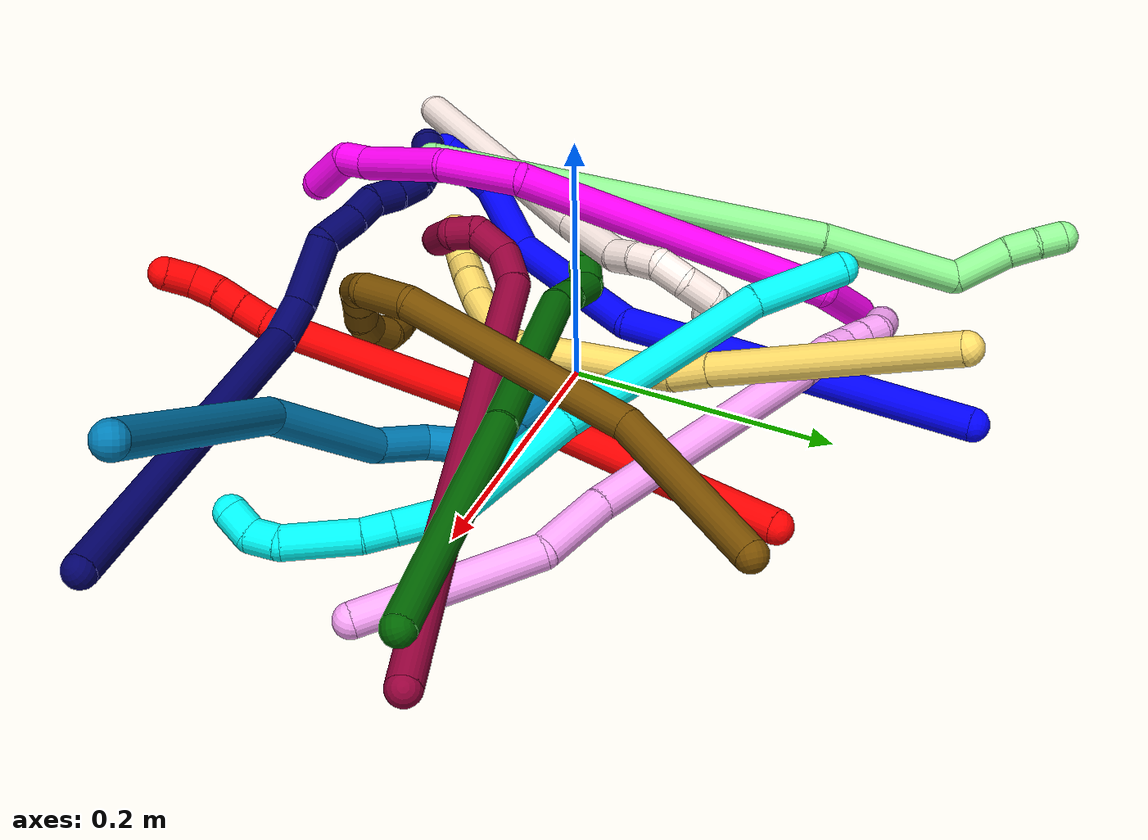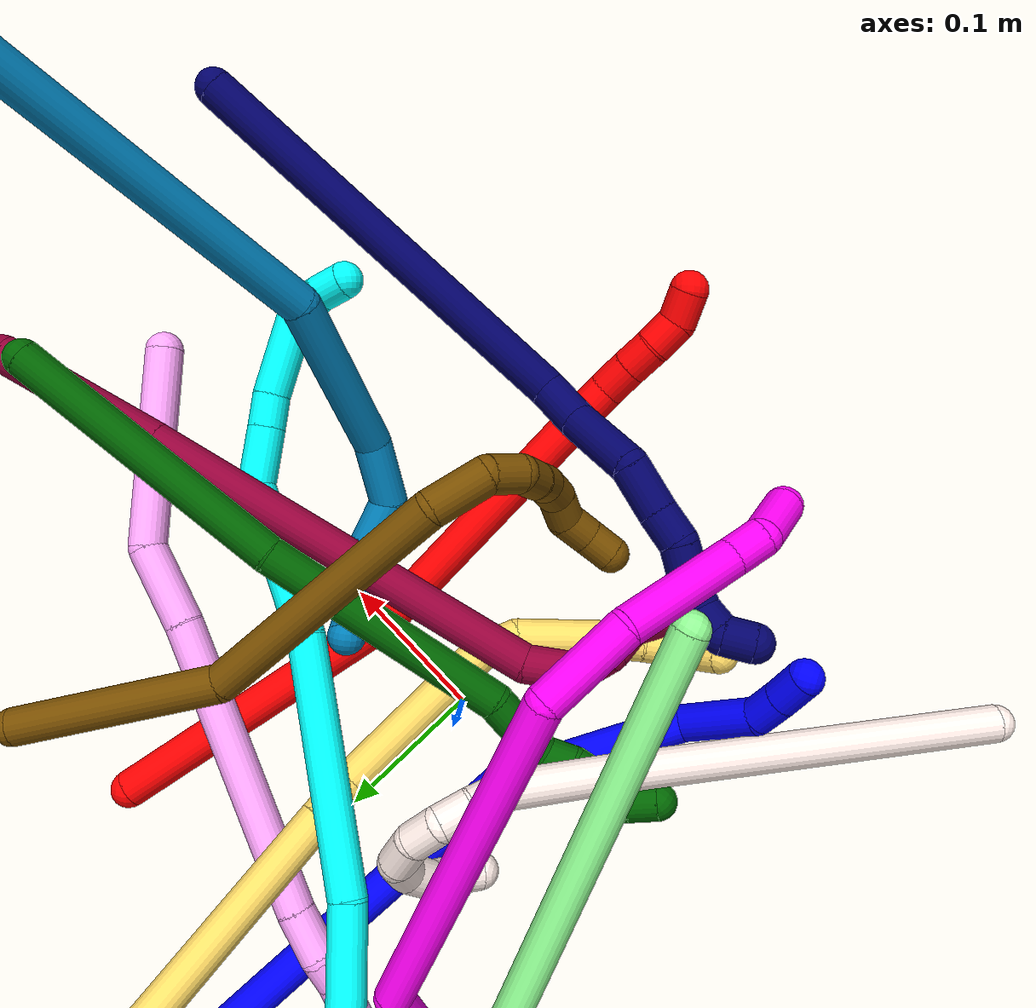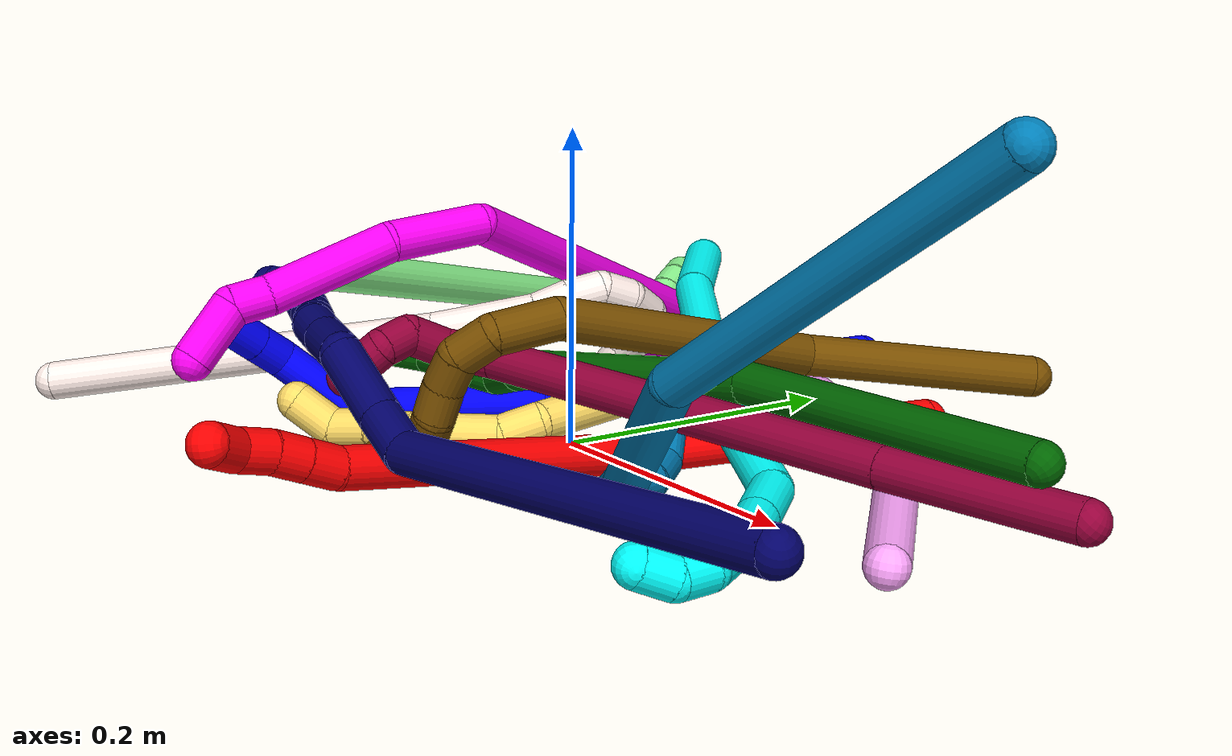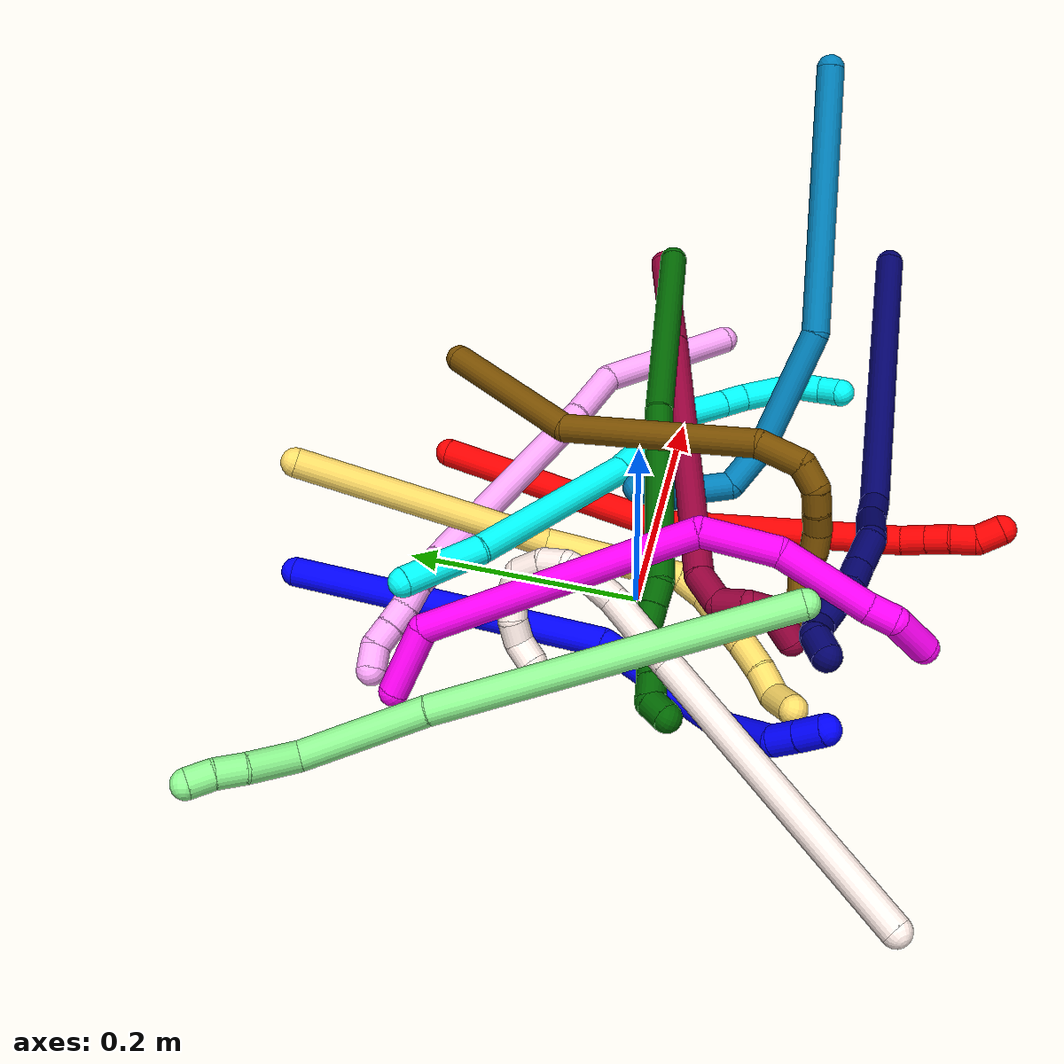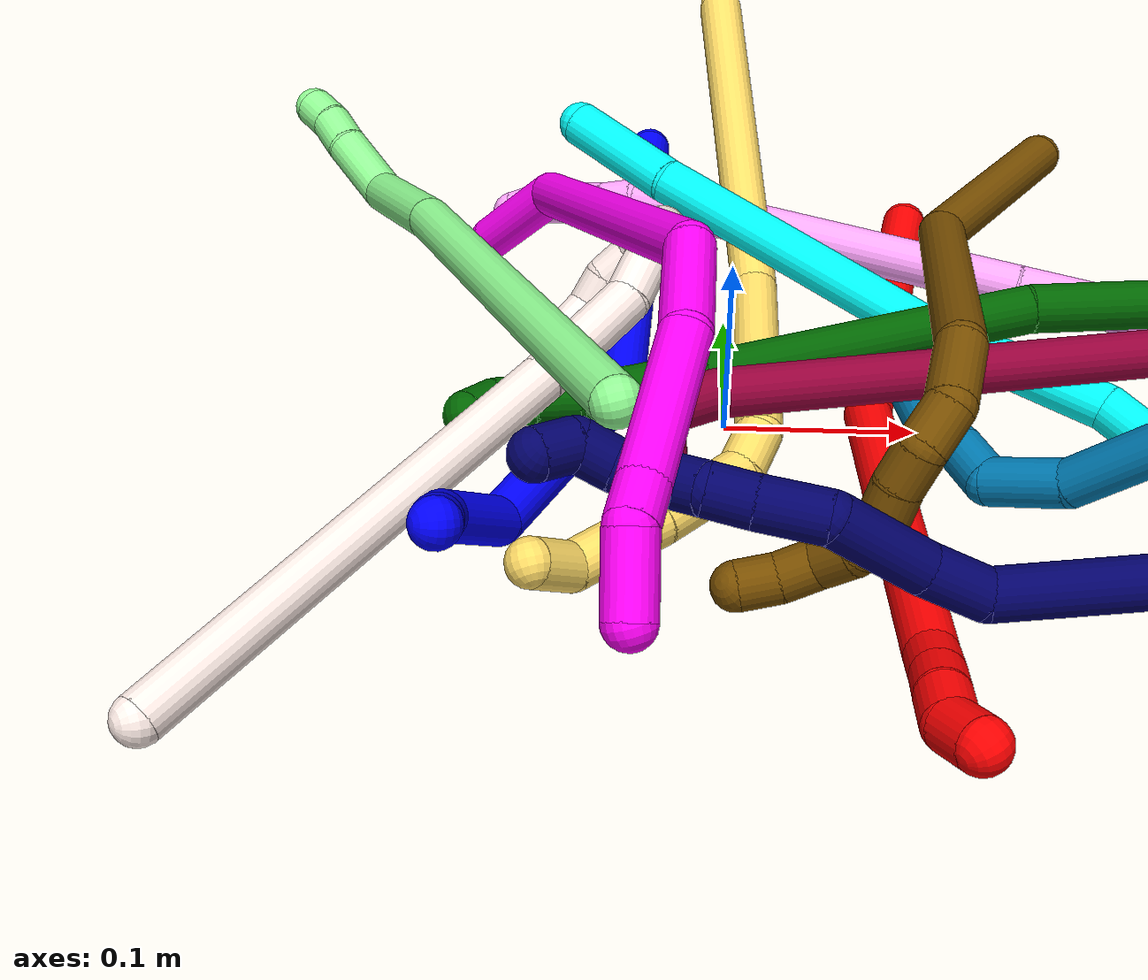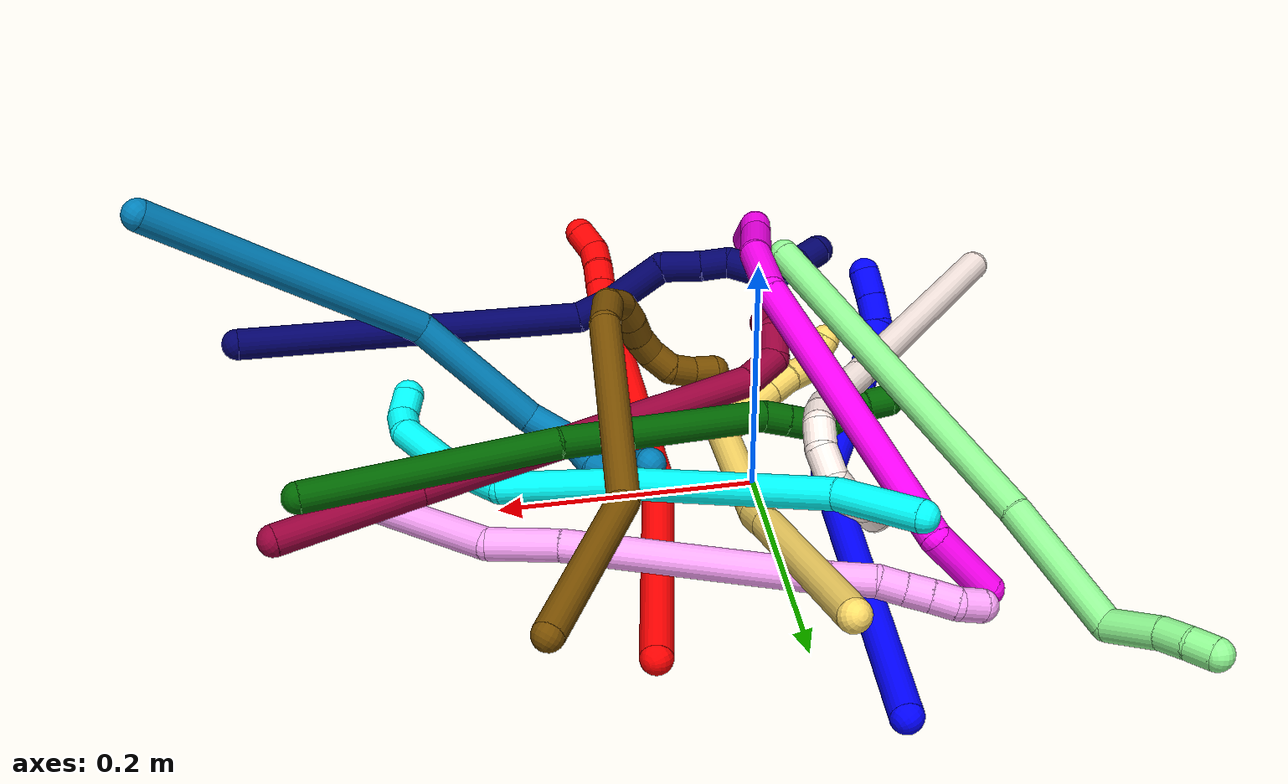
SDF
<sdf version="1.7">
 <world name="default">
  <plugin name="TubeGeneratorPlugin" filename="libtube_generator_plugin.so"/>
  <model name="photoneo_s_sensor">
   <static>1</static>
   <pose>0 0 2 1.57079 1.57079 3.14159</pose>
   <link name="link">
    <inertial><mass>0.1</mass></inertial>
    <sensor name="sensor" type="depth">
     <update_rate>30</update_rate>
     <camera>
      <horizontal_fov>1.22</horizontal_fov>
      <image><width>1920</width><height>1200</height><format>B8G8R8</format></image>
      <clip><near>0.1</near><far>4</far></clip>
      <depth_camera><output>points</output></depth_camera>
     </camera>
     <plugin name="camera_plugin" filename="libgazebo_ros_depth_camera.so">
      <baseline>0.2</baseline>
      <alwaysOn>1</alwaysOn>
      <updateRate>0.0</updateRate>
      <cameraName>camera_ir</cameraName>
      <imageTopicName>/camera/color/image_raw</imageTopicName>
      <cameraInfoTopicName>/camera/color/camera_info</cameraInfoTopicName>
      <depthImageTopicName>/camera/depth/image_raw</depthImageTopicName>
      <depthImageCameraInfoTopicName>/camera/depth/camera_info</depthImageCameraInfoTopicName>
      <pointCloudTopicName>/camera/depth/points</pointCloudTopicName>
      <frameName>fr_optical</frameName>
      <pointCloudCutoff>0.1</pointCloudCutoff>
      <pointCloudCutoffMax>2.0</pointCloudCutoffMax>
      <distortionK1>0</distortionK1>
      <distortionK2>0</distortionK2>
      <distortionK3>0</distortionK3>
      <distortionT1>0</distortionT1>
      <distortionT2>0</distortionT2>
      <CxPrime>0</CxPrime>
      <Cx>0</Cx>
      <Cy>0</Cy>
      <focalLength>0</focalLength>
      <hackBaseline>0</hackBaseline>
     </plugin>
    </sensor>
   </link>
  </model>
  <gravity>0 0 -9.8</gravity>
  <magnetic_field>6e-06 2.3e-05 -4.2e-05</magnetic_field>
  <atmosphere type="adiabatic"/>
  <physics name="default_physics" default="0" type="ode">
   <max_step_size>0.003</max_step_size>
   <real_time_factor>1</real_time_factor>
   <real_time_update_rate>1000</real_time_update_rate>
   <max_contacts>10000</max_contacts>
   <ode>
    <solver>
     <type>quick</type>
     <iters>100</iters>
     <sor>1.3</sor>
     <use_dynamic_moi_rescaling>0</use_dynamic_moi_rescaling>
    </solver>
    <constraints>
     <contact_max_correcting_vel>0</contact_max_correcting_vel>
     <contact_surface_layer>0.001</contact_surface_layer>
     <cfm>0</cfm>
     <erp>0.2</erp>
    </constraints>
   </ode>
  </physics>
  <scene><ambient>0.4 0.4 0.4 1</ambient><background>0.7 0.7 0.7 1</background><shadows>0</shadows></scene>
  <audio><device>default</device></audio>
  <spherical_coordinates>
   <surface_model>EARTH_WGS84</surface_model>
   <latitude_deg>0</latitude_deg>
   <longitude_deg>0</longitude_deg>
   <elevation>0</elevation>
   <heading_deg>0</heading_deg>
  </spherical_coordinates>
  <model name="bin">
   <static>1</static>
   <link name="bottom">
    <collision name="collision-bottom">
     <pose>0 0 -0.01 0 -0 0</pose>
     <geometry><box><size>0.8 0.6 0.02</size></box></geometry>
     <surface>
      <friction><ode><mu>100</mu><mu2>100</mu2></ode></friction>
      <contact><collide_bitmask>65535</collide_bitmask></contact>
     </surface>
    </collision>
   </link>
   <link name="west_wall">
    <collision name="collision-west_wall">
     <pose>-0.41 0 0.1 0 -0 0</pose>
     <geometry><box><size>0.02 0.6 0.2</size></box></geometry>
     <surface>
      <friction><ode><mu>100</mu><mu2>100</mu2></ode></friction>
      <contact><collide_bitmask>65535</collide_bitmask></contact>
     </surface>
    </collision>
   </link>
   <link name="east_wall">
    <collision name="collision-east_wall">
     <pose>0.41 0 0.1 0 -0 0</pose>
     <geometry><box><size>0.02 0.6 0.2</size></box></geometry>
     <surface>
      <friction><ode><mu>100</mu><mu2>100</mu2></ode></friction>
      <contact><collide_bitmask>65535</collide_bitmask></contact>
     </surface>
    </collision>
   </link>
   <link name="south_wall">
    <collision name="collision-south_wall">
     <pose>0 -0.31 0.1 0 -0 0</pose>
     <geometry><box><size>0.8 0.02 0.2</size></box></geometry>
     <surface>
      <friction><ode><mu>100</mu><mu2>100</mu2></ode></friction>
      <contact><collide_bitmask>65535</collide_bitmask></contact>
     </surface>
    </collision>
   </link>
   <link name="north_wall">
    <collision name="collision-north_wall">
     <pose>0 0.31 0.1 0 -0 0</pose>
     <geometry><box><size>0.8 0.02 0.2</size></box></geometry>
     <surface>
      <friction><ode><mu>100</mu><mu2>100</mu2></ode></friction>
      <contact><collide_bitmask>65535</collide_bitmask></contact>
     </surface>
    </collision>
   </link>
  </model>
  <model name="1">
   <static>0</static>
   <link name="1">
    <collision name="collision-cylinder-e_1_1_4">
     <pose>-0.046354 -0.108998 -0.06722 2.12341 -0.347299 -0.608998</pose>
     <geometry><cylinder><radius>0.0125</radius><length>0.272381</length></cylinder></geometry>
     <surface>
      <friction><ode><mu>1.16</mu><mu2>1.16</mu2><slip1>0</slip1><slip2>0</slip2></ode></friction>
      <contact><ode><kp>1e+06</kp><kd>1</kd><max_vel>0</max_vel><min_depth>0.001</min_depth></ode></contact>
     </surface>
    </collision>
    <visual name="visual-cylinder-e_1_1_4">
     <pose>-0.046354 -0.108998 -0.06722 2.12341 -0.347299 -0.608998</pose>
     <geometry><cylinder><radius>0.0125</radius><length>0.272381</length></cylinder></geometry>
     <material><ambient>0 0 1 1</ambient></material>
    </visual>
    <collision name="collision-cylinder-e_2_4_5">
     <pose>-0.100843 -0.2555 -0.184369 2.49736 -0.12956 -0.383961</pose>
     <geometry><cylinder><radius>0.0125</radius><length>0.125946</length></cylinder></geometry>
     <surface>
      <friction><ode><mu>1.16</mu><mu2>1.16</mu2><slip1>0</slip1><slip2>0</slip2></ode></friction>
      <contact><ode><kp>1e+06</kp><kd>1</kd><max_vel>0</max_vel><min_depth>0.001</min_depth></ode></contact>
     </surface>
    </collision>
    <visual name="visual-cylinder-e_2_4_5">
     <pose>-0.100843 -0.2555 -0.184369 2.49736 -0.12956 -0.383961</pose>
     <geometry><cylinder><radius>0.0125</radius><length>0.125946</length></cylinder></geometry>
     <material><ambient>0 0 1 1</ambient></material>
    </visual>
    <collision name="collision-cylinder-e_3_5_6">
     <pose>-0.124962 -0.296587 -0.256625 2.98247 -0.615266 -2.64985</pose>
     <geometry><cylinder><radius>0.0125</radius><length>0.055382</length></cylinder></geometry>
     <surface>
      <friction><ode><mu>1.16</mu><mu2>1.16</mu2><slip1>0</slip1><slip2>0</slip2></ode></friction>
      <contact><ode><kp>1e+06</kp><kd>1</kd><max_vel>0</max_vel><min_depth>0.001</min_depth></ode></contact>
     </surface>
    </collision>
    <visual name="visual-cylinder-e_3_5_6">
     <pose>-0.124962 -0.296587 -0.256625 2.98247 -0.615266 -2.64985</pose>
     <geometry><cylinder><radius>0.0125</radius><length>0.055382</length></cylinder></geometry>
     <material><ambient>0 0 1 1</ambient></material>
    </visual>
    <collision name="collision-cylinder-e_4_6_7">
     <pose>-0.150026 -0.304545 -0.284566 2.47958 -0.906036 -1.91216</pose>
     <geometry><cylinder><radius>0.0125</radius><length>0.023077</length></cylinder></geometry>
     <surface>
      <friction><ode><mu>1.16</mu><mu2>1.16</mu2><slip1>0</slip1><slip2>0</slip2></ode></friction>
      <contact><ode><kp>1e+06</kp><kd>1</kd><max_vel>0</max_vel><min_depth>0.001</min_depth></ode></contact>
     </surface>
    </collision>
    <visual name="visual-cylinder-e_4_6_7">
     <pose>-0.150026 -0.304545 -0.284566 2.47958 -0.906036 -1.91216</pose>
     <geometry><cylinder><radius>0.0125</radius><length>0.023077</length></cylinder></geometry>
     <material><ambient>0 0 1 1</ambient></material>
    </visual>
    <collision name="collision-cylinder-e_5_7_2">
     <pose>-0.168447 -0.313467 -0.295361 2.42131 -0.934996 -1.8598</pose>
     <geometry><cylinder><radius>0.0125</radius><length>0.023214</length></cylinder></geometry>
     <surface>
      <friction><ode><mu>1.16</mu><mu2>1.16</mu2><slip1>0</slip1><slip2>0</slip2></ode></friction>
      <contact><ode><kp>1e+06</kp><kd>1</kd><max_vel>0</max_vel><min_depth>0.001</min_depth></ode></contact>
     </surface>
    </collision>
    <visual name="visual-cylinder-e_5_7_2">
     <pose>-0.168447 -0.313467 -0.295361 2.42131 -0.934996 -1.8598</pose>
     <geometry><cylinder><radius>0.0125</radius><length>0.023214</length></cylinder></geometry>
     <material><ambient>0 0 1 1</ambient></material>
    </visual>
    <collision name="collision-sphere-2">
     <pose>-0.177786 -0.318013 -0.300542 0 -0 0</pose>
     <geometry><sphere><radius>0.0125</radius></sphere></geometry>
     <surface>
      <friction><ode><mu>1.16</mu><mu2>1.16</mu2><slip1>0</slip1><slip2>0</slip2></ode></friction>
      <contact><ode><kp>1e+06</kp><kd>1</kd><max_vel>0</max_vel><min_depth>0.001</min_depth></ode></contact>
     </surface>
    </collision>
    <visual name="visual-sphere-2">
     <pose>-0.177786 -0.318013 -0.300542 0 -0 0</pose>
     <geometry><sphere><radius>0.0125</radius></sphere></geometry>
     <material><ambient>0 0 1 1</ambient></material>
    </visual>
    <collision name="collision-sphere-7">
     <pose>-0.159107 -0.308921 -0.290181 0 -0 0</pose>
     <geometry><sphere><radius>0.0125</radius></sphere></geometry>
     <surface>
      <friction><ode><mu>1.16</mu><mu2>1.16</mu2><slip1>0</slip1><slip2>0</slip2></ode></friction>
      <contact><ode><kp>1e+06</kp><kd>1</kd><max_vel>0</max_vel><min_depth>0.001</min_depth></ode></contact>
     </surface>
    </collision>
    <visual name="visual-sphere-7">
     <pose>-0.159107 -0.308921 -0.290181 0 -0 0</pose>
     <geometry><sphere><radius>0.0125</radius></sphere></geometry>
     <material><ambient>0 0 1 1</ambient></material>
    </visual>
    <collision name="collision-sphere-6">
     <pose>-0.140944 -0.30017 -0.278952 0 -0 0</pose>
     <geometry><sphere><radius>0.0125</radius></sphere></geometry>
     <surface>
      <friction><ode><mu>1.16</mu><mu2>1.16</mu2><slip1>0</slip1><slip2>0</slip2></ode></friction>
      <contact><ode><kp>1e+06</kp><kd>1</kd><max_vel>0</max_vel><min_depth>0.001</min_depth></ode></contact>
     </surface>
    </collision>
    <visual name="visual-sphere-6">
     <pose>-0.140944 -0.30017 -0.278952 0 -0 0</pose>
     <geometry><sphere><radius>0.0125</radius></sphere></geometry>
     <material><ambient>0 0 1 1</ambient></material>
    </visual>
    <collision name="collision-sphere-5">
     <pose>-0.108979 -0.293004 -0.234298 0 -0 0</pose>
     <geometry><sphere><radius>0.0125</radius></sphere></geometry>
     <surface>
      <friction><ode><mu>1.16</mu><mu2>1.16</mu2><slip1>0</slip1><slip2>0</slip2></ode></friction>
      <contact><ode><kp>1e+06</kp><kd>1</kd><max_vel>0</max_vel><min_depth>0.001</min_depth></ode></contact>
     </surface>
    </collision>
    <visual name="visual-sphere-5">
     <pose>-0.108979 -0.293004 -0.234298 0 -0 0</pose>
     <geometry><sphere><radius>0.0125</radius></sphere></geometry>
     <material><ambient>0 0 1 1</ambient></material>
    </visual>
    <collision name="collision-sphere-1">
     <geometry><sphere><radius>0.0125</radius></sphere></geometry>
     <surface>
      <friction><ode><mu>1.16</mu><mu2>1.16</mu2><slip1>0</slip1><slip2>0</slip2></ode></friction>
      <contact><ode><kp>1e+06</kp><kd>1</kd><max_vel>0</max_vel><min_depth>0.001</min_depth></ode></contact>
     </surface>
    </collision>
    <visual name="visual-sphere-1">
     <geometry><sphere><radius>0.0125</radius></sphere></geometry>
     <material><ambient>0 0 1 1</ambient></material>
    </visual>
    <collision name="collision-sphere-4">
     <pose>-0.092707 -0.217996 -0.13444 0 -0 0</pose>
     <geometry><sphere><radius>0.0125</radius></sphere></geometry>
     <surface>
      <friction><ode><mu>1.16</mu><mu2>1.16</mu2><slip1>0</slip1><slip2>0</slip2></ode></friction>
      <contact><ode><kp>1e+06</kp><kd>1</kd><max_vel>0</max_vel><min_depth>0.001</min_depth></ode></contact>
     </surface>
    </collision>
    <visual name="visual-sphere-4">
     <pose>-0.092707 -0.217996 -0.13444 0 -0 0</pose>
     <geometry><sphere><radius>0.0125</radius></sphere></geometry>
     <material><ambient>0 0 1 1</ambient></material>
    </visual>
    <inertial>
     <pose>-0.07924 -0.185197 -0.138332 0 -0 0</pose>
     <mass>0.5</mass>
     <inertia>
      <ixx>0.000455</ixx>
      <ixy>0</ixy>
      <ixz>0</ixz>
      <iyy>-0.001562</iyy>
      <iyz>0</iyz>
      <izz>0.00205</izz>
     </inertia>
    </inertial>
   </link>
   <pose>-0.047008 0.287422 0.012381 2.02069 0.977215 2.45386</pose>
  </model>
  <model name="2">
   <static>0</static>
   <link name="2">
    <collision name="collision-cylinder-e_1_1_4">
     <pose>-0.006441 -0.065038 0.077579 0.697688 -0.063538 -0.023117</pose>
     <geometry><cylinder><radius>0.0125</radius><length>0.202879</length></cylinder></geometry>
     <surface>
      <friction><ode><mu>1.16</mu><mu2>1.16</mu2><slip1>0</slip1><slip2>0</slip2></ode></friction>
      <contact><ode><kp>1e+06</kp><kd>1</kd><max_vel>0</max_vel><min_depth>0.001</min_depth></ode></contact>
     </surface>
    </collision>
    <visual name="visual-cylinder-e_1_1_4">
     <pose>-0.006441 -0.065038 0.077579 0.697688 -0.063538 -0.023117</pose>
     <geometry><cylinder><radius>0.0125</radius><length>0.202879</length></cylinder></geometry>
     <material><ambient>1 0 0 1</ambient></material>
    </visual>
    <collision name="collision-cylinder-e_2_4_5">
     <pose>-0.012893 -0.216288 0.216952 0.948904 -0.000104 -5.3e-05</pose>
     <geometry><cylinder><radius>0.0125</radius><length>0.212141</length></cylinder></geometry>
     <surface>
      <friction><ode><mu>1.16</mu><mu2>1.16</mu2><slip1>0</slip1><slip2>0</slip2></ode></friction>
      <contact><ode><kp>1e+06</kp><kd>1</kd><max_vel>0</max_vel><min_depth>0.001</min_depth></ode></contact>
     </surface>
    </collision>
    <visual name="visual-cylinder-e_2_4_5">
     <pose>-0.012893 -0.216288 0.216952 0.948904 -0.000104 -5.3e-05</pose>
     <geometry><cylinder><radius>0.0125</radius><length>0.212141</length></cylinder></geometry>
     <material><ambient>1 0 0 1</ambient></material>
    </visual>
    <collision name="collision-cylinder-e_3_5_6">
     <pose>-0.010224 -0.311122 0.284792 0.959309 0.249205 0.13012</pose>
     <geometry><cylinder><radius>0.0125</radius><length>0.021735</length></cylinder></geometry>
     <surface>
      <friction><ode><mu>1.16</mu><mu2>1.16</mu2><slip1>0</slip1><slip2>0</slip2></ode></friction>
      <contact><ode><kp>1e+06</kp><kd>1</kd><max_vel>0</max_vel><min_depth>0.001</min_depth></ode></contact>
     </surface>
    </collision>
    <visual name="visual-cylinder-e_3_5_6">
     <pose>-0.010224 -0.311122 0.284792 0.959309 0.249205 0.13012</pose>
     <geometry><cylinder><radius>0.0125</radius><length>0.021735</length></cylinder></geometry>
     <material><ambient>1 0 0 1</ambient></material>
    </visual>
    <collision name="collision-cylinder-e_4_6_7">
     <pose>-0.005039 -0.327556 0.296635 0.932325 0.252033 0.127313</pose>
     <geometry><cylinder><radius>0.0125</radius><length>0.020088</length></cylinder></geometry>
     <surface>
      <friction><ode><mu>1.16</mu><mu2>1.16</mu2><slip1>0</slip1><slip2>0</slip2></ode></friction>
      <contact><ode><kp>1e+06</kp><kd>1</kd><max_vel>0</max_vel><min_depth>0.001</min_depth></ode></contact>
     </surface>
    </collision>
    <visual name="visual-cylinder-e_4_6_7">
     <pose>-0.005039 -0.327556 0.296635 0.932325 0.252033 0.127313</pose>
     <geometry><cylinder><radius>0.0125</radius><length>0.020088</length></cylinder></geometry>
     <material><ambient>1 0 0 1</ambient></material>
    </visual>
    <collision name="collision-cylinder-e_5_7_8">
     <pose>-0.001655 -0.343928 0.308673 0.940886 0.082744 0.042095</pose>
     <geometry><cylinder><radius>0.0125</radius><length>0.021262</length></cylinder></geometry>
     <surface>
      <friction><ode><mu>1.16</mu><mu2>1.16</mu2><slip1>0</slip1><slip2>0</slip2></ode></friction>
      <contact><ode><kp>1e+06</kp><kd>1</kd><max_vel>0</max_vel><min_depth>0.001</min_depth></ode></contact>
     </surface>
    </collision>
    <visual name="visual-cylinder-e_5_7_8">
     <pose>-0.001655 -0.343928 0.308673 0.940886 0.082744 0.042095</pose>
     <geometry><cylinder><radius>0.0125</radius><length>0.021262</length></cylinder></geometry>
     <material><ambient>1 0 0 1</ambient></material>
    </visual>
    <collision name="collision-cylinder-e_6_8_2">
     <pose>0.000784 -0.363175 0.316717 1.40365 0.143059 0.121003</pose>
     <geometry><cylinder><radius>0.0125</radius><length>0.021896</length></cylinder></geometry>
     <surface>
      <friction><ode><mu>1.16</mu><mu2>1.16</mu2><slip1>0</slip1><slip2>0</slip2></ode></friction>
      <contact><ode><kp>1e+06</kp><kd>1</kd><max_vel>0</max_vel><min_depth>0.001</min_depth></ode></contact>
     </surface>
    </collision>
    <visual name="visual-cylinder-e_6_8_2">
     <pose>0.000784 -0.363175 0.316717 1.40365 0.143059 0.121003</pose>
     <geometry><cylinder><radius>0.0125</radius><length>0.021896</length></cylinder></geometry>
     <material><ambient>1 0 0 1</ambient></material>
    </visual>
    <collision name="collision-sphere-2">
     <pose>0.002345 -0.37386 0.318519 0 -0 0</pose>
     <geometry><sphere><radius>0.0125</radius></sphere></geometry>
     <surface>
      <friction><ode><mu>1.16</mu><mu2>1.16</mu2><slip1>0</slip1><slip2>0</slip2></ode></friction>
      <contact><ode><kp>1e+06</kp><kd>1</kd><max_vel>0</max_vel><min_depth>0.001</min_depth></ode></contact>
     </surface>
    </collision>
    <visual name="visual-sphere-2">
     <pose>0.002345 -0.37386 0.318519 0 -0 0</pose>
     <geometry><sphere><radius>0.0125</radius></sphere></geometry>
     <material><ambient>1 0 0 1</ambient></material>
    </visual>
    <collision name="collision-sphere-4">
     <pose>-0.012882 -0.130076 0.155158 0 -0 0</pose>
     <geometry><sphere><radius>0.0125</radius></sphere></geometry>
     <surface>
      <friction><ode><mu>1.16</mu><mu2>1.16</mu2><slip1>0</slip1><slip2>0</slip2></ode></friction>
      <contact><ode><kp>1e+06</kp><kd>1</kd><max_vel>0</max_vel><min_depth>0.001</min_depth></ode></contact>
     </surface>
    </collision>
    <visual name="visual-sphere-4">
     <pose>-0.012882 -0.130076 0.155158 0 -0 0</pose>
     <geometry><sphere><radius>0.0125</radius></sphere></geometry>
     <material><ambient>1 0 0 1</ambient></material>
    </visual>
    <collision name="collision-sphere-1">
     <geometry><sphere><radius>0.0125</radius></sphere></geometry>
     <surface>
      <friction><ode><mu>1.16</mu><mu2>1.16</mu2><slip1>0</slip1><slip2>0</slip2></ode></friction>
      <contact><ode><kp>1e+06</kp><kd>1</kd><max_vel>0</max_vel><min_depth>0.001</min_depth></ode></contact>
     </surface>
    </collision>
    <visual name="visual-sphere-1">
     <geometry><sphere><radius>0.0125</radius></sphere></geometry>
     <material><ambient>1 0 0 1</ambient></material>
    </visual>
    <collision name="collision-sphere-8">
     <pose>-0.000777 -0.35249 0.314914 0 -0 0</pose>
     <geometry><sphere><radius>0.0125</radius></sphere></geometry>
     <surface>
      <friction><ode><mu>1.16</mu><mu2>1.16</mu2><slip1>0</slip1><slip2>0</slip2></ode></friction>
      <contact><ode><kp>1e+06</kp><kd>1</kd><max_vel>0</max_vel><min_depth>0.001</min_depth></ode></contact>
     </surface>
    </collision>
    <visual name="visual-sphere-8">
     <pose>-0.000777 -0.35249 0.314914 0 -0 0</pose>
     <geometry><sphere><radius>0.0125</radius></sphere></geometry>
     <material><ambient>1 0 0 1</ambient></material>
    </visual>
    <collision name="collision-sphere-5">
     <pose>-0.012904 -0.302499 0.278746 0 -0 0</pose>
     <geometry><sphere><radius>0.0125</radius></sphere></geometry>
     <surface>
      <friction><ode><mu>1.16</mu><mu2>1.16</mu2><slip1>0</slip1><slip2>0</slip2></ode></friction>
      <contact><ode><kp>1e+06</kp><kd>1</kd><max_vel>0</max_vel><min_depth>0.001</min_depth></ode></contact>
     </surface>
    </collision>
    <visual name="visual-sphere-5">
     <pose>-0.012904 -0.302499 0.278746 0 -0 0</pose>
     <geometry><sphere><radius>0.0125</radius></sphere></geometry>
     <material><ambient>1 0 0 1</ambient></material>
    </visual>
    <collision name="collision-sphere-6">
     <pose>-0.007543 -0.319746 0.290838 0 -0 0</pose>
     <geometry><sphere><radius>0.0125</radius></sphere></geometry>
     <surface>
      <friction><ode><mu>1.16</mu><mu2>1.16</mu2><slip1>0</slip1><slip2>0</slip2></ode></friction>
      <contact><ode><kp>1e+06</kp><kd>1</kd><max_vel>0</max_vel><min_depth>0.001</min_depth></ode></contact>
     </surface>
    </collision>
    <visual name="visual-sphere-6">
     <pose>-0.007543 -0.319746 0.290838 0 -0 0</pose>
     <geometry><sphere><radius>0.0125</radius></sphere></geometry>
     <material><ambient>1 0 0 1</ambient></material>
    </visual>
    <collision name="collision-sphere-7">
     <pose>-0.002534 -0.335367 0.302432 0 -0 0</pose>
     <geometry><sphere><radius>0.0125</radius></sphere></geometry>
     <surface>
      <friction><ode><mu>1.16</mu><mu2>1.16</mu2><slip1>0</slip1><slip2>0</slip2></ode></friction>
      <contact><ode><kp>1e+06</kp><kd>1</kd><max_vel>0</max_vel><min_depth>0.001</min_depth></ode></contact>
     </surface>
    </collision>
    <visual name="visual-sphere-7">
     <pose>-0.002534 -0.335367 0.302432 0 -0 0</pose>
     <geometry><sphere><radius>0.0125</radius></sphere></geometry>
     <material><ambient>1 0 0 1</ambient></material>
    </visual>
    <inertial>
     <pose>-0.008766 -0.17537 0.17482 0 -0 0</pose>
     <mass>0.5</mass>
     <inertia>
      <ixx>0.001497</ixx>
      <ixy>0</ixy>
      <ixz>0</ixz>
      <iyy>0.000967</iyy>
      <iyz>0</iyz>
      <izz>0.001179</izz>
     </inertia>
    </inertial>
   </link>
   <pose>0.110398 0.199268 0.011647 -2.06073 -1.27538 2.74801</pose>
  </model>
  <model name="3">
   <static>0</static>
   <link name="3">
    <collision name="collision-cylinder-e_1_1_4">
     <pose>0.004541 -0.006014 -0.034045 2.96673 0.130597 1.28191</pose>
     <geometry><cylinder><radius>0.0125</radius><length>0.069739</length></cylinder></geometry>
     <surface>
      <friction><ode><mu>1.16</mu><mu2>1.16</mu2><slip1>0</slip1><slip2>0</slip2></ode></friction>
      <contact><ode><kp>1e+06</kp><kd>1</kd><max_vel>0</max_vel><min_depth>0.001</min_depth></ode></contact>
     </surface>
    </collision>
    <visual name="visual-cylinder-e_1_1_4">
     <pose>0.004541 -0.006014 -0.034045 2.96673 0.130597 1.28191</pose>
     <geometry><cylinder><radius>0.0125</radius><length>0.069739</length></cylinder></geometry>
     <material><ambient>0.003922 1 0.996078 1</ambient></material>
    </visual>
    <collision name="collision-cylinder-e_2_4_5">
     <pose>0.002968 -0.031341 -0.147945 2.90431 -0.074276 -0.604323</pose>
     <geometry><cylinder><radius>0.0125</radius><length>0.164768</length></cylinder></geometry>
     <surface>
      <friction><ode><mu>1.16</mu><mu2>1.16</mu2><slip1>0</slip1><slip2>0</slip2></ode></friction>
      <contact><ode><kp>1e+06</kp><kd>1</kd><max_vel>0</max_vel><min_depth>0.001</min_depth></ode></contact>
     </surface>
    </collision>
    <visual name="visual-cylinder-e_2_4_5">
     <pose>0.002968 -0.031341 -0.147945 2.90431 -0.074276 -0.604323</pose>
     <geometry><cylinder><radius>0.0125</radius><length>0.164768</length></cylinder></geometry>
     <material><ambient>0.003922 1 0.996078 1</ambient></material>
    </visual>
    <collision name="collision-cylinder-e_3_5_6">
     <pose>-0.015205 -0.061009 -0.278224 2.93901 -0.230136 -1.69899</pose>
     <geometry><cylinder><radius>0.0125</radius><length>0.10574</length></cylinder></geometry>
     <surface>
      <friction><ode><mu>1.16</mu><mu2>1.16</mu2><slip1>0</slip1><slip2>0</slip2></ode></friction>
      <contact><ode><kp>1e+06</kp><kd>1</kd><max_vel>0</max_vel><min_depth>0.001</min_depth></ode></contact>
     </surface>
    </collision>
    <visual name="visual-cylinder-e_3_5_6">
     <pose>-0.015205 -0.061009 -0.278224 2.93901 -0.230136 -1.69899</pose>
     <geometry><cylinder><radius>0.0125</radius><length>0.10574</length></cylinder></geometry>
     <material><ambient>0.003922 1 0.996078 1</ambient></material>
    </visual>
    <collision name="collision-cylinder-e_4_6_7">
     <pose>-0.021892 -0.074625 -0.347183 2.96753 0.278154 2.02682</pose>
     <geometry><cylinder><radius>0.0125</radius><length>0.039144</length></cylinder></geometry>
     <surface>
      <friction><ode><mu>1.16</mu><mu2>1.16</mu2><slip1>0</slip1><slip2>0</slip2></ode></friction>
      <contact><ode><kp>1e+06</kp><kd>1</kd><max_vel>0</max_vel><min_depth>0.001</min_depth></ode></contact>
     </surface>
    </collision>
    <visual name="visual-cylinder-e_4_6_7">
     <pose>-0.021892 -0.074625 -0.347183 2.96753 0.278154 2.02682</pose>
     <geometry><cylinder><radius>0.0125</radius><length>0.039144</length></cylinder></geometry>
     <material><ambient>0.003922 1 0.996078 1</ambient></material>
    </visual>
    <collision name="collision-cylinder-e_5_7_8">
     <pose>-0.013511 -0.079561 -0.376437 2.98645 0.2703 2.10304</pose>
     <geometry><cylinder><radius>0.0125</radius><length>0.022515</length></cylinder></geometry>
     <surface>
      <friction><ode><mu>1.16</mu><mu2>1.16</mu2><slip1>0</slip1><slip2>0</slip2></ode></friction>
      <contact><ode><kp>1e+06</kp><kd>1</kd><max_vel>0</max_vel><min_depth>0.001</min_depth></ode></contact>
     </surface>
    </collision>
    <visual name="visual-cylinder-e_5_7_8">
     <pose>-0.013511 -0.079561 -0.376437 2.98645 0.2703 2.10304</pose>
     <geometry><cylinder><radius>0.0125</radius><length>0.022515</length></cylinder></geometry>
     <material><ambient>0.003922 1 0.996078 1</ambient></material>
    </visual>
    <collision name="collision-cylinder-e_6_8_9">
     <pose>0.001144 -0.083749 -0.411687 3.03956 0.441326 2.69394</pose>
     <geometry><cylinder><radius>0.0125</radius><length>0.054546</length></cylinder></geometry>
     <surface>
      <friction><ode><mu>1.16</mu><mu2>1.16</mu2><slip1>0</slip1><slip2>0</slip2></ode></friction>
      <contact><ode><kp>1e+06</kp><kd>1</kd><max_vel>0</max_vel><min_depth>0.001</min_depth></ode></contact>
     </surface>
    </collision>
    <visual name="visual-cylinder-e_6_8_9">
     <pose>0.001144 -0.083749 -0.411687 3.03956 0.441326 2.69394</pose>
     <geometry><cylinder><radius>0.0125</radius><length>0.054546</length></cylinder></geometry>
     <material><ambient>0.003922 1 0.996078 1</ambient></material>
    </visual>
    <collision name="collision-cylinder-e_7_9_10">
     <pose>0.021431 -0.087742 -0.442727 2.91785 0.912878 2.69177</pose>
     <geometry><cylinder><radius>0.0125</radius><length>0.021832</length></cylinder></geometry>
     <surface>
      <friction><ode><mu>1.16</mu><mu2>1.16</mu2><slip1>0</slip1><slip2>0</slip2></ode></friction>
      <contact><ode><kp>1e+06</kp><kd>1</kd><max_vel>0</max_vel><min_depth>0.001</min_depth></ode></contact>
     </surface>
    </collision>
    <visual name="visual-cylinder-e_7_9_10">
     <pose>0.021431 -0.087742 -0.442727 2.91785 0.912878 2.69177</pose>
     <geometry><cylinder><radius>0.0125</radius><length>0.021832</length></cylinder></geometry>
     <material><ambient>0.003922 1 0.996078 1</ambient></material>
    </visual>
    <collision name="collision-cylinder-e_8_10_2">
     <pose>0.040235 -0.086436 -0.451835 -2.32148 1.21219 -2.02129</pose>
     <geometry><cylinder><radius>0.0125</radius><length>0.021716</length></cylinder></geometry>
     <surface>
      <friction><ode><mu>1.16</mu><mu2>1.16</mu2><slip1>0</slip1><slip2>0</slip2></ode></friction>
      <contact><ode><kp>1e+06</kp><kd>1</kd><max_vel>0</max_vel><min_depth>0.001</min_depth></ode></contact>
     </surface>
    </collision>
    <visual name="visual-cylinder-e_8_10_2">
     <pose>0.040235 -0.086436 -0.451835 -2.32148 1.21219 -2.02129</pose>
     <geometry><cylinder><radius>0.0125</radius><length>0.021716</length></cylinder></geometry>
     <material><ambient>0.003922 1 0.996078 1</ambient></material>
    </visual>
    <collision name="collision-sphere-2">
     <pose>0.050403 -0.083649 -0.454434 0 -0 0</pose>
     <geometry><sphere><radius>0.0125</radius></sphere></geometry>
     <surface>
      <friction><ode><mu>1.16</mu><mu2>1.16</mu2><slip1>0</slip1><slip2>0</slip2></ode></friction>
      <contact><ode><kp>1e+06</kp><kd>1</kd><max_vel>0</max_vel><min_depth>0.001</min_depth></ode></contact>
     </surface>
    </collision>
    <visual name="visual-sphere-2">
     <pose>0.050403 -0.083649 -0.454434 0 -0 0</pose>
     <geometry><sphere><radius>0.0125</radius></sphere></geometry>
     <material><ambient>0.003922 1 0.996078 1</ambient></material>
    </visual>
    <collision name="collision-sphere-10">
     <pose>0.030068 -0.089223 -0.449235 0 -0 0</pose>
     <geometry><sphere><radius>0.0125</radius></sphere></geometry>
     <surface>
      <friction><ode><mu>1.16</mu><mu2>1.16</mu2><slip1>0</slip1><slip2>0</slip2></ode></friction>
      <contact><ode><kp>1e+06</kp><kd>1</kd><max_vel>0</max_vel><min_depth>0.001</min_depth></ode></contact>
     </surface>
    </collision>
    <visual name="visual-sphere-10">
     <pose>0.030068 -0.089223 -0.449235 0 -0 0</pose>
     <geometry><sphere><radius>0.0125</radius></sphere></geometry>
     <material><ambient>0.003922 1 0.996078 1</ambient></material>
    </visual>
    <collision name="collision-sphere-9">
     <pose>0.012793 -0.086261 -0.436219 0 -0 0</pose>
     <geometry><sphere><radius>0.0125</radius></sphere></geometry>
     <surface>
      <friction><ode><mu>1.16</mu><mu2>1.16</mu2><slip1>0</slip1><slip2>0</slip2></ode></friction>
      <contact><ode><kp>1e+06</kp><kd>1</kd><max_vel>0</max_vel><min_depth>0.001</min_depth></ode></contact>
     </surface>
    </collision>
    <visual name="visual-sphere-9">
     <pose>0.012793 -0.086261 -0.436219 0 -0 0</pose>
     <geometry><sphere><radius>0.0125</radius></sphere></geometry>
     <material><ambient>0.003922 1 0.996078 1</ambient></material>
    </visual>
    <collision name="collision-sphere-4">
     <pose>0.009082 -0.012029 -0.06809 0 -0 0</pose>
     <geometry><sphere><radius>0.0125</radius></sphere></geometry>
     <surface>
      <friction><ode><mu>1.16</mu><mu2>1.16</mu2><slip1>0</slip1><slip2>0</slip2></ode></friction>
      <contact><ode><kp>1e+06</kp><kd>1</kd><max_vel>0</max_vel><min_depth>0.001</min_depth></ode></contact>
     </surface>
    </collision>
    <visual name="visual-sphere-4">
     <pose>0.009082 -0.012029 -0.06809 0 -0 0</pose>
     <geometry><sphere><radius>0.0125</radius></sphere></geometry>
     <material><ambient>0.003922 1 0.996078 1</ambient></material>
    </visual>
    <collision name="collision-sphere-1">
     <geometry><sphere><radius>0.0125</radius></sphere></geometry>
     <surface>
      <friction><ode><mu>1.16</mu><mu2>1.16</mu2><slip1>0</slip1><slip2>0</slip2></ode></friction>
      <contact><ode><kp>1e+06</kp><kd>1</kd><max_vel>0</max_vel><min_depth>0.001</min_depth></ode></contact>
     </surface>
    </collision>
    <visual name="visual-sphere-1">
     <geometry><sphere><radius>0.0125</radius></sphere></geometry>
     <material><ambient>0.003922 1 0.996078 1</ambient></material>
    </visual>
    <collision name="collision-sphere-8">
     <pose>-0.010506 -0.081237 -0.387155 0 -0 0</pose>
     <geometry><sphere><radius>0.0125</radius></sphere></geometry>
     <surface>
      <friction><ode><mu>1.16</mu><mu2>1.16</mu2><slip1>0</slip1><slip2>0</slip2></ode></friction>
      <contact><ode><kp>1e+06</kp><kd>1</kd><max_vel>0</max_vel><min_depth>0.001</min_depth></ode></contact>
     </surface>
    </collision>
    <visual name="visual-sphere-8">
     <pose>-0.010506 -0.081237 -0.387155 0 -0 0</pose>
     <geometry><sphere><radius>0.0125</radius></sphere></geometry>
     <material><ambient>0.003922 1 0.996078 1</ambient></material>
    </visual>
    <collision name="collision-sphere-5">
     <pose>-0.003145 -0.050652 -0.2278 0 -0 0</pose>
     <geometry><sphere><radius>0.0125</radius></sphere></geometry>
     <surface>
      <friction><ode><mu>1.16</mu><mu2>1.16</mu2><slip1>0</slip1><slip2>0</slip2></ode></friction>
      <contact><ode><kp>1e+06</kp><kd>1</kd><max_vel>0</max_vel><min_depth>0.001</min_depth></ode></contact>
     </surface>
    </collision>
    <visual name="visual-sphere-5">
     <pose>-0.003145 -0.050652 -0.2278 0 -0 0</pose>
     <geometry><sphere><radius>0.0125</radius></sphere></geometry>
     <material><ambient>0.003922 1 0.996078 1</ambient></material>
    </visual>
    <collision name="collision-sphere-6">
     <pose>-0.027266 -0.071366 -0.328648 0 -0 0</pose>
     <geometry><sphere><radius>0.0125</radius></sphere></geometry>
     <surface>
      <friction><ode><mu>1.16</mu><mu2>1.16</mu2><slip1>0</slip1><slip2>0</slip2></ode></friction>
      <contact><ode><kp>1e+06</kp><kd>1</kd><max_vel>0</max_vel><min_depth>0.001</min_depth></ode></contact>
     </surface>
    </collision>
    <visual name="visual-sphere-6">
     <pose>-0.027266 -0.071366 -0.328648 0 -0 0</pose>
     <geometry><sphere><radius>0.0125</radius></sphere></geometry>
     <material><ambient>0.003922 1 0.996078 1</ambient></material>
    </visual>
    <collision name="collision-sphere-7">
     <pose>-0.016517 -0.077884 -0.365719 0 -0 0</pose>
     <geometry><sphere><radius>0.0125</radius></sphere></geometry>
     <surface>
      <friction><ode><mu>1.16</mu><mu2>1.16</mu2><slip1>0</slip1><slip2>0</slip2></ode></friction>
      <contact><ode><kp>1e+06</kp><kd>1</kd><max_vel>0</max_vel><min_depth>0.001</min_depth></ode></contact>
     </surface>
    </collision>
    <visual name="visual-sphere-7">
     <pose>-0.016517 -0.077884 -0.365719 0 -0 0</pose>
     <geometry><sphere><radius>0.0125</radius></sphere></geometry>
     <material><ambient>0.003922 1 0.996078 1</ambient></material>
    </visual>
    <inertial>
     <pose>-0.001118 -0.050215 -0.240339 0 -0 0</pose>
     <mass>0.5</mass>
     <inertia>
      <ixx>2.2e-05</ixx>
      <ixy>0</ixy>
      <ixz>0</ixz>
      <iyy>-0.000546</iyy>
      <iyz>0</iyz>
      <izz>0.000117</izz>
     </inertia>
    </inertial>
   </link>
   <pose>-0.085053 0.170275 0.088941 1.58926 -0.12422 -2.17306</pose>
  </model>
  <model name="4">
   <static>0</static>
   <link name="4">
    <collision name="collision-cylinder-e_1_1_4">
     <pose>-0.018534 -0.061307 0.016933 1.30132 -0.283551 -0.216461</pose>
     <geometry><cylinder><radius>0.0125</radius><length>0.132496</length></cylinder></geometry>
     <surface>
      <friction><ode><mu>1.16</mu><mu2>1.16</mu2><slip1>0</slip1><slip2>0</slip2></ode></friction>
      <contact><ode><kp>1e+06</kp><kd>1</kd><max_vel>0</max_vel><min_depth>0.001</min_depth></ode></contact>
     </surface>
    </collision>
    <visual name="visual-cylinder-e_1_1_4">
     <pose>-0.018534 -0.061307 0.016933 1.30132 -0.283551 -0.216461</pose>
     <geometry><cylinder><radius>0.0125</radius><length>0.132496</length></cylinder></geometry>
     <material><ambient>1 0.65098 0.996078 1</ambient></material>
    </visual>
    <collision name="collision-cylinder-e_2_4_5">
     <pose>-0.031446 -0.149423 0.036951 1.4562 0.205402 0.183248</pose>
     <geometry><cylinder><radius>0.0125</radius><length>0.055129</length></cylinder></geometry>
     <surface>
      <friction><ode><mu>1.16</mu><mu2>1.16</mu2><slip1>0</slip1><slip2>0</slip2></ode></friction>
      <contact><ode><kp>1e+06</kp><kd>1</kd><max_vel>0</max_vel><min_depth>0.001</min_depth></ode></contact>
     </surface>
    </collision>
    <visual name="visual-cylinder-e_2_4_5">
     <pose>-0.031446 -0.149423 0.036951 1.4562 0.205402 0.183248</pose>
     <geometry><cylinder><radius>0.0125</radius><length>0.055129</length></cylinder></geometry>
     <material><ambient>1 0.65098 0.996078 1</ambient></material>
    </visual>
    <collision name="collision-cylinder-e_3_5_6">
     <pose>-0.015265 -0.274552 0.047587 1.49415 0.106664 0.0988</pose>
     <geometry><cylinder><radius>0.0125</radius><length>0.198349</length></cylinder></geometry>
     <surface>
      <friction><ode><mu>1.16</mu><mu2>1.16</mu2><slip1>0</slip1><slip2>0</slip2></ode></friction>
      <contact><ode><kp>1e+06</kp><kd>1</kd><max_vel>0</max_vel><min_depth>0.001</min_depth></ode></contact>
     </surface>
    </collision>
    <visual name="visual-cylinder-e_3_5_6">
     <pose>-0.015265 -0.274552 0.047587 1.49415 0.106664 0.0988</pose>
     <geometry><cylinder><radius>0.0125</radius><length>0.198349</length></cylinder></geometry>
     <material><ambient>1 0.65098 0.996078 1</ambient></material>
    </visual>
    <collision name="collision-cylinder-e_4_6_7">
     <pose>-0.001377 -0.389097 0.055997 1.51786 0.202163 0.191801</pose>
     <geometry><cylinder><radius>0.0125</radius><length>0.03317</length></cylinder></geometry>
     <surface>
      <friction><ode><mu>1.16</mu><mu2>1.16</mu2><slip1>0</slip1><slip2>0</slip2></ode></friction>
      <contact><ode><kp>1e+06</kp><kd>1</kd><max_vel>0</max_vel><min_depth>0.001</min_depth></ode></contact>
     </surface>
    </collision>
    <visual name="visual-cylinder-e_4_6_7">
     <pose>-0.001377 -0.389097 0.055997 1.51786 0.202163 0.191801</pose>
     <geometry><cylinder><radius>0.0125</radius><length>0.03317</length></cylinder></geometry>
     <material><ambient>1 0.65098 0.996078 1</ambient></material>
    </visual>
    <collision name="collision-cylinder-e_5_7_8">
     <pose>0.003786 -0.415219 0.054279 1.8256 0.177378 0.229094</pose>
     <geometry><cylinder><radius>0.0125</radius><length>0.02078</length></cylinder></geometry>
     <surface>
      <friction><ode><mu>1.16</mu><mu2>1.16</mu2><slip1>0</slip1><slip2>0</slip2></ode></friction>
      <contact><ode><kp>1e+06</kp><kd>1</kd><max_vel>0</max_vel><min_depth>0.001</min_depth></ode></contact>
     </surface>
    </collision>
    <visual name="visual-cylinder-e_5_7_8">
     <pose>0.003786 -0.415219 0.054279 1.8256 0.177378 0.229094</pose>
     <geometry><cylinder><radius>0.0125</radius><length>0.02078</length></cylinder></geometry>
     <material><ambient>1 0.65098 0.996078 1</ambient></material>
    </visual>
    <collision name="collision-cylinder-e_6_8_9">
     <pose>0.006659 -0.434997 0.050412 1.70059 0.103947 0.118365</pose>
     <geometry><cylinder><radius>0.0125</radius><length>0.020038</length></cylinder></geometry>
     <surface>
      <friction><ode><mu>1.16</mu><mu2>1.16</mu2><slip1>0</slip1><slip2>0</slip2></ode></friction>
      <contact><ode><kp>1e+06</kp><kd>1</kd><max_vel>0</max_vel><min_depth>0.001</min_depth></ode></contact>
     </surface>
    </collision>
    <visual name="visual-cylinder-e_6_8_9">
     <pose>0.006659 -0.434997 0.050412 1.70059 0.103947 0.118365</pose>
     <geometry><cylinder><radius>0.0125</radius><length>0.020038</length></cylinder></geometry>
     <material><ambient>1 0.65098 0.996078 1</ambient></material>
    </visual>
    <collision name="collision-cylinder-e_7_9_10">
     <pose>0.008456 -0.454748 0.0476 1.72381 0.075632 0.088175</pose>
     <geometry><cylinder><radius>0.0125</radius><length>0.02003</length></cylinder></geometry>
     <surface>
      <friction><ode><mu>1.16</mu><mu2>1.16</mu2><slip1>0</slip1><slip2>0</slip2></ode></friction>
      <contact><ode><kp>1e+06</kp><kd>1</kd><max_vel>0</max_vel><min_depth>0.001</min_depth></ode></contact>
     </surface>
    </collision>
    <visual name="visual-cylinder-e_7_9_10">
     <pose>0.008456 -0.454748 0.0476 1.72381 0.075632 0.088175</pose>
     <geometry><cylinder><radius>0.0125</radius><length>0.02003</length></cylinder></geometry>
     <material><ambient>1 0.65098 0.996078 1</ambient></material>
    </visual>
    <collision name="collision-cylinder-e_8_10_2">
     <pose>0.014028 -0.472746 0.042789 1.9553 0.502223 0.727229</pose>
     <geometry><cylinder><radius>0.0125</radius><length>0.020007</length></cylinder></geometry>
     <surface>
      <friction><ode><mu>1.16</mu><mu2>1.16</mu2><slip1>0</slip1><slip2>0</slip2></ode></friction>
      <contact><ode><kp>1e+06</kp><kd>1</kd><max_vel>0</max_vel><min_depth>0.001</min_depth></ode></contact>
     </surface>
    </collision>
    <visual name="visual-cylinder-e_8_10_2">
     <pose>0.014028 -0.472746 0.042789 1.9553 0.502223 0.727229</pose>
     <geometry><cylinder><radius>0.0125</radius><length>0.020007</length></cylinder></geometry>
     <material><ambient>1 0.65098 0.996078 1</ambient></material>
    </visual>
    <collision name="collision-sphere-2">
     <pose>0.018843 -0.480874 0.039499 0 -0 0</pose>
     <geometry><sphere><radius>0.0125</radius></sphere></geometry>
     <surface>
      <friction><ode><mu>1.16</mu><mu2>1.16</mu2><slip1>0</slip1><slip2>0</slip2></ode></friction>
      <contact><ode><kp>1e+06</kp><kd>1</kd><max_vel>0</max_vel><min_depth>0.001</min_depth></ode></contact>
     </surface>
    </collision>
    <visual name="visual-sphere-2">
     <pose>0.018843 -0.480874 0.039499 0 -0 0</pose>
     <geometry><sphere><radius>0.0125</radius></sphere></geometry>
     <material><ambient>1 0.65098 0.996078 1</ambient></material>
    </visual>
    <collision name="collision-sphere-10">
     <pose>0.009212 -0.464618 0.046078 0 -0 0</pose>
     <geometry><sphere><radius>0.0125</radius></sphere></geometry>
     <surface>
      <friction><ode><mu>1.16</mu><mu2>1.16</mu2><slip1>0</slip1><slip2>0</slip2></ode></friction>
      <contact><ode><kp>1e+06</kp><kd>1</kd><max_vel>0</max_vel><min_depth>0.001</min_depth></ode></contact>
     </surface>
    </collision>
    <visual name="visual-sphere-10">
     <pose>0.009212 -0.464618 0.046078 0 -0 0</pose>
     <geometry><sphere><radius>0.0125</radius></sphere></geometry>
     <material><ambient>1 0.65098 0.996078 1</ambient></material>
    </visual>
    <collision name="collision-sphere-9">
     <pose>0.007699 -0.444878 0.049122 0 -0 0</pose>
     <geometry><sphere><radius>0.0125</radius></sphere></geometry>
     <surface>
      <friction><ode><mu>1.16</mu><mu2>1.16</mu2><slip1>0</slip1><slip2>0</slip2></ode></friction>
      <contact><ode><kp>1e+06</kp><kd>1</kd><max_vel>0</max_vel><min_depth>0.001</min_depth></ode></contact>
     </surface>
    </collision>
    <visual name="visual-sphere-9">
     <pose>0.007699 -0.444878 0.049122 0 -0 0</pose>
     <geometry><sphere><radius>0.0125</radius></sphere></geometry>
     <material><ambient>1 0.65098 0.996078 1</ambient></material>
    </visual>
    <collision name="collision-sphere-4">
     <pose>-0.037068 -0.122614 0.033865 0 -0 0</pose>
     <geometry><sphere><radius>0.0125</radius></sphere></geometry>
     <surface>
      <friction><ode><mu>1.16</mu><mu2>1.16</mu2><slip1>0</slip1><slip2>0</slip2></ode></friction>
      <contact><ode><kp>1e+06</kp><kd>1</kd><max_vel>0</max_vel><min_depth>0.001</min_depth></ode></contact>
     </surface>
    </collision>
    <visual name="visual-sphere-4">
     <pose>-0.037068 -0.122614 0.033865 0 -0 0</pose>
     <geometry><sphere><radius>0.0125</radius></sphere></geometry>
     <material><ambient>1 0.65098 0.996078 1</ambient></material>
    </visual>
    <collision name="collision-sphere-1">
     <geometry><sphere><radius>0.0125</radius></sphere></geometry>
     <surface>
      <friction><ode><mu>1.16</mu><mu2>1.16</mu2><slip1>0</slip1><slip2>0</slip2></ode></friction>
      <contact><ode><kp>1e+06</kp><kd>1</kd><max_vel>0</max_vel><min_depth>0.001</min_depth></ode></contact>
     </surface>
    </collision>
    <visual name="visual-sphere-1">
     <geometry><sphere><radius>0.0125</radius></sphere></geometry>
     <material><ambient>1 0.65098 0.996078 1</ambient></material>
    </visual>
    <collision name="collision-sphere-8">
     <pose>0.00562 -0.425116 0.051701 0 -0 0</pose>
     <geometry><sphere><radius>0.0125</radius></sphere></geometry>
     <surface>
      <friction><ode><mu>1.16</mu><mu2>1.16</mu2><slip1>0</slip1><slip2>0</slip2></ode></friction>
      <contact><ode><kp>1e+06</kp><kd>1</kd><max_vel>0</max_vel><min_depth>0.001</min_depth></ode></contact>
     </surface>
    </collision>
    <visual name="visual-sphere-8">
     <pose>0.00562 -0.425116 0.051701 0 -0 0</pose>
     <geometry><sphere><radius>0.0125</radius></sphere></geometry>
     <material><ambient>1 0.65098 0.996078 1</ambient></material>
    </visual>
    <collision name="collision-sphere-5">
     <pose>-0.025824 -0.176231 0.040037 0 -0 0</pose>
     <geometry><sphere><radius>0.0125</radius></sphere></geometry>
     <surface>
      <friction><ode><mu>1.16</mu><mu2>1.16</mu2><slip1>0</slip1><slip2>0</slip2></ode></friction>
      <contact><ode><kp>1e+06</kp><kd>1</kd><max_vel>0</max_vel><min_depth>0.001</min_depth></ode></contact>
     </surface>
    </collision>
    <visual name="visual-sphere-5">
     <pose>-0.025824 -0.176231 0.040037 0 -0 0</pose>
     <geometry><sphere><radius>0.0125</radius></sphere></geometry>
     <material><ambient>1 0.65098 0.996078 1</ambient></material>
    </visual>
    <collision name="collision-sphere-6">
     <pose>-0.004707 -0.372873 0.055138 0 -0 0</pose>
     <geometry><sphere><radius>0.0125</radius></sphere></geometry>
     <surface>
      <friction><ode><mu>1.16</mu><mu2>1.16</mu2><slip1>0</slip1><slip2>0</slip2></ode></friction>
      <contact><ode><kp>1e+06</kp><kd>1</kd><max_vel>0</max_vel><min_depth>0.001</min_depth></ode></contact>
     </surface>
    </collision>
    <visual name="visual-sphere-6">
     <pose>-0.004707 -0.372873 0.055138 0 -0 0</pose>
     <geometry><sphere><radius>0.0125</radius></sphere></geometry>
     <material><ambient>1 0.65098 0.996078 1</ambient></material>
    </visual>
    <collision name="collision-sphere-7">
     <pose>0.001953 -0.405322 0.056857 0 -0 0</pose>
     <geometry><sphere><radius>0.0125</radius></sphere></geometry>
     <surface>
      <friction><ode><mu>1.16</mu><mu2>1.16</mu2><slip1>0</slip1><slip2>0</slip2></ode></friction>
      <contact><ode><kp>1e+06</kp><kd>1</kd><max_vel>0</max_vel><min_depth>0.001</min_depth></ode></contact>
     </surface>
    </collision>
    <visual name="visual-sphere-7">
     <pose>0.001953 -0.405322 0.056857 0 -0 0</pose>
     <geometry><sphere><radius>0.0125</radius></sphere></geometry>
     <material><ambient>1 0.65098 0.996078 1</ambient></material>
    </visual>
    <inertial>
     <pose>-0.013201 -0.239272 0.039049 0 -0 0</pose>
     <mass>0.5</mass>
     <inertia>
      <ixx>0.000893</ixx>
      <ixy>0</ixy>
      <ixz>0</ixz>
      <iyy>0.000114</iyy>
      <iyz>0</iyz>
      <izz>0.000845</izz>
     </inertia>
    </inertial>
   </link>
   <pose>0.307381 -0.017367 0.012265 0.077057 -0.149604 -2.05537</pose>
  </model>
  <model name="5">
   <static>0</static>
   <link name="5">
    <collision name="collision-cylinder-e_1_1_4">
     <pose>-0.004509 -0.034042 -0.087375 2.77008 -0.048049 -0.254354</pose>
     <geometry><cylinder><radius>0.0125</radius><length>0.187762</length></cylinder></geometry>
     <surface>
      <friction><ode><mu>1.16</mu><mu2>1.16</mu2><slip1>0</slip1><slip2>0</slip2></ode></friction>
      <contact><ode><kp>1e+06</kp><kd>1</kd><max_vel>0</max_vel><min_depth>0.001</min_depth></ode></contact>
     </surface>
    </collision>
    <visual name="visual-cylinder-e_1_1_4">
     <pose>-0.004509 -0.034042 -0.087375 2.77008 -0.048049 -0.254354</pose>
     <geometry><cylinder><radius>0.0125</radius><length>0.187762</length></cylinder></geometry>
     <material><ambient>1 0.858824 0.4 1</ambient></material>
    </visual>
    <collision name="collision-cylinder-e_2_4_5">
     <pose>-0.010077 -0.072911 -0.189249 2.82019 -0.069185 -0.420661</pose>
     <geometry><cylinder><radius>0.0125</radius><length>0.030635</length></cylinder></geometry>
     <surface>
      <friction><ode><mu>1.16</mu><mu2>1.16</mu2><slip1>0</slip1><slip2>0</slip2></ode></friction>
      <contact><ode><kp>1e+06</kp><kd>1</kd><max_vel>0</max_vel><min_depth>0.001</min_depth></ode></contact>
     </surface>
    </collision>
    <visual name="visual-cylinder-e_2_4_5">
     <pose>-0.010077 -0.072911 -0.189249 2.82019 -0.069185 -0.420661</pose>
     <geometry><cylinder><radius>0.0125</radius><length>0.030635</length></cylinder></geometry>
     <material><ambient>1 0.858824 0.4 1</ambient></material>
    </visual>
    <collision name="collision-cylinder-e_3_5_6">
     <pose>-0.012451 -0.111535 -0.251789 2.52854 -0.022384 -0.070697</pose>
     <geometry><cylinder><radius>0.0125</radius><length>0.117506</length></cylinder></geometry>
     <surface>
      <friction><ode><mu>1.16</mu><mu2>1.16</mu2><slip1>0</slip1><slip2>0</slip2></ode></friction>
      <contact><ode><kp>1e+06</kp><kd>1</kd><max_vel>0</max_vel><min_depth>0.001</min_depth></ode></contact>
     </surface>
    </collision>
    <visual name="visual-cylinder-e_3_5_6">
     <pose>-0.012451 -0.111535 -0.251789 2.52854 -0.022384 -0.070697</pose>
     <geometry><cylinder><radius>0.0125</radius><length>0.117506</length></cylinder></geometry>
     <material><ambient>1 0.858824 0.4 1</ambient></material>
    </visual>
    <collision name="collision-cylinder-e_4_6_7">
     <pose>-0.01933 -0.152166 -0.309361 2.51942 -0.442972 -1.22192</pose>
     <geometry><cylinder><radius>0.0125</radius><length>0.025962</length></cylinder></geometry>
     <surface>
      <friction><ode><mu>1.16</mu><mu2>1.16</mu2><slip1>0</slip1><slip2>0</slip2></ode></friction>
      <contact><ode><kp>1e+06</kp><kd>1</kd><max_vel>0</max_vel><min_depth>0.001</min_depth></ode></contact>
     </surface>
    </collision>
    <visual name="visual-cylinder-e_4_6_7">
     <pose>-0.01933 -0.152166 -0.309361 2.51942 -0.442972 -1.22192</pose>
     <geometry><cylinder><radius>0.0125</radius><length>0.025962</length></cylinder></geometry>
     <material><ambient>1 0.858824 0.4 1</ambient></material>
    </visual>
    <collision name="collision-cylinder-e_5_7_8">
     <pose>-0.042435 -0.178926 -0.328763 2.03081 -0.66789 -1.01958</pose>
     <geometry><cylinder><radius>0.0125</radius><length>0.056644</length></cylinder></geometry>
     <surface>
      <friction><ode><mu>1.16</mu><mu2>1.16</mu2><slip1>0</slip1><slip2>0</slip2></ode></friction>
      <contact><ode><kp>1e+06</kp><kd>1</kd><max_vel>0</max_vel><min_depth>0.001</min_depth></ode></contact>
     </surface>
    </collision>
    <visual name="visual-cylinder-e_5_7_8">
     <pose>-0.042435 -0.178926 -0.328763 2.03081 -0.66789 -1.01958</pose>
     <geometry><cylinder><radius>0.0125</radius><length>0.056644</length></cylinder></geometry>
     <material><ambient>1 0.858824 0.4 1</ambient></material>
    </visual>
    <collision name="collision-cylinder-e_6_8_9">
     <pose>-0.068815 -0.208668 -0.342231 1.92191 -0.701875 -0.965283</pose>
     <geometry><cylinder><radius>0.0125</radius><length>0.027382</length></cylinder></geometry>
     <surface>
      <friction><ode><mu>1.16</mu><mu2>1.16</mu2><slip1>0</slip1><slip2>0</slip2></ode></friction>
      <contact><ode><kp>1e+06</kp><kd>1</kd><max_vel>0</max_vel><min_depth>0.001</min_depth></ode></contact>
     </surface>
    </collision>
    <visual name="visual-cylinder-e_6_8_9">
     <pose>-0.068815 -0.208668 -0.342231 1.92191 -0.701875 -0.965283</pose>
     <geometry><cylinder><radius>0.0125</radius><length>0.027382</length></cylinder></geometry>
     <material><ambient>1 0.858824 0.4 1</ambient></material>
    </visual>
    <collision name="collision-cylinder-e_7_9_10">
     <pose>-0.087029 -0.226045 -0.34941 2.01336 -0.842148 -1.23196</pose>
     <geometry><cylinder><radius>0.0125</radius><length>0.025128</length></cylinder></geometry>
     <surface>
      <friction><ode><mu>1.16</mu><mu2>1.16</mu2><slip1>0</slip1><slip2>0</slip2></ode></friction>
      <contact><ode><kp>1e+06</kp><kd>1</kd><max_vel>0</max_vel><min_depth>0.001</min_depth></ode></contact>
     </surface>
    </collision>
    <visual name="visual-cylinder-e_7_9_10">
     <pose>-0.087029 -0.226045 -0.34941 2.01336 -0.842148 -1.23196</pose>
     <geometry><cylinder><radius>0.0125</radius><length>0.025128</length></cylinder></geometry>
     <material><ambient>1 0.858824 0.4 1</ambient></material>
    </visual>
    <collision name="collision-cylinder-e_8_10_2">
     <pose>-0.100479 -0.247464 -0.351852 1.48866 -0.28515 -0.26291</pose>
     <geometry><cylinder><radius>0.0125</radius><length>0.028981</length></cylinder></geometry>
     <surface>
      <friction><ode><mu>1.16</mu><mu2>1.16</mu2><slip1>0</slip1><slip2>0</slip2></ode></friction>
      <contact><ode><kp>1e+06</kp><kd>1</kd><max_vel>0</max_vel><min_depth>0.001</min_depth></ode></contact>
     </surface>
    </collision>
    <visual name="visual-cylinder-e_8_10_2">
     <pose>-0.100479 -0.247464 -0.351852 1.48866 -0.28515 -0.26291</pose>
     <geometry><cylinder><radius>0.0125</radius><length>0.028981</length></cylinder></geometry>
     <material><ambient>1 0.858824 0.4 1</ambient></material>
    </visual>
    <collision name="collision-sphere-2">
     <pose>-0.104555 -0.261322 -0.350711 0 -0 0</pose>
     <geometry><sphere><radius>0.0125</radius></sphere></geometry>
     <surface>
      <friction><ode><mu>1.16</mu><mu2>1.16</mu2><slip1>0</slip1><slip2>0</slip2></ode></friction>
      <contact><ode><kp>1e+06</kp><kd>1</kd><max_vel>0</max_vel><min_depth>0.001</min_depth></ode></contact>
     </surface>
    </collision>
    <visual name="visual-sphere-2">
     <pose>-0.104555 -0.261322 -0.350711 0 -0 0</pose>
     <geometry><sphere><radius>0.0125</radius></sphere></geometry>
     <material><ambient>1 0.858824 0.4 1</ambient></material>
    </visual>
    <collision name="collision-sphere-10">
     <pose>-0.096403 -0.233605 -0.352993 0 -0 0</pose>
     <geometry><sphere><radius>0.0125</radius></sphere></geometry>
     <surface>
      <friction><ode><mu>1.16</mu><mu2>1.16</mu2><slip1>0</slip1><slip2>0</slip2></ode></friction>
      <contact><ode><kp>1e+06</kp><kd>1</kd><max_vel>0</max_vel><min_depth>0.001</min_depth></ode></contact>
     </surface>
    </collision>
    <visual name="visual-sphere-10">
     <pose>-0.096403 -0.233605 -0.352993 0 -0 0</pose>
     <geometry><sphere><radius>0.0125</radius></sphere></geometry>
     <material><ambient>1 0.858824 0.4 1</ambient></material>
    </visual>
    <collision name="collision-sphere-9">
     <pose>-0.077655 -0.218485 -0.345827 0 -0 0</pose>
     <geometry><sphere><radius>0.0125</radius></sphere></geometry>
     <surface>
      <friction><ode><mu>1.16</mu><mu2>1.16</mu2><slip1>0</slip1><slip2>0</slip2></ode></friction>
      <contact><ode><kp>1e+06</kp><kd>1</kd><max_vel>0</max_vel><min_depth>0.001</min_depth></ode></contact>
     </surface>
    </collision>
    <visual name="visual-sphere-9">
     <pose>-0.077655 -0.218485 -0.345827 0 -0 0</pose>
     <geometry><sphere><radius>0.0125</radius></sphere></geometry>
     <material><ambient>1 0.858824 0.4 1</ambient></material>
    </visual>
    <collision name="collision-sphere-4">
     <pose>-0.009018 -0.068084 -0.17475 0 -0 0</pose>
     <geometry><sphere><radius>0.0125</radius></sphere></geometry>
     <surface>
      <friction><ode><mu>1.16</mu><mu2>1.16</mu2><slip1>0</slip1><slip2>0</slip2></ode></friction>
      <contact><ode><kp>1e+06</kp><kd>1</kd><max_vel>0</max_vel><min_depth>0.001</min_depth></ode></contact>
     </surface>
    </collision>
    <visual name="visual-sphere-4">
     <pose>-0.009018 -0.068084 -0.17475 0 -0 0</pose>
     <geometry><sphere><radius>0.0125</radius></sphere></geometry>
     <material><ambient>1 0.858824 0.4 1</ambient></material>
    </visual>
    <collision name="collision-sphere-1">
     <geometry><sphere><radius>0.0125</radius></sphere></geometry>
     <surface>
      <friction><ode><mu>1.16</mu><mu2>1.16</mu2><slip1>0</slip1><slip2>0</slip2></ode></friction>
      <contact><ode><kp>1e+06</kp><kd>1</kd><max_vel>0</max_vel><min_depth>0.001</min_depth></ode></contact>
     </surface>
    </collision>
    <visual name="visual-sphere-1">
     <geometry><sphere><radius>0.0125</radius></sphere></geometry>
     <material><ambient>1 0.858824 0.4 1</ambient></material>
    </visual>
    <collision name="collision-sphere-8">
     <pose>-0.059976 -0.198851 -0.338635 0 -0 0</pose>
     <geometry><sphere><radius>0.0125</radius></sphere></geometry>
     <surface>
      <friction><ode><mu>1.16</mu><mu2>1.16</mu2><slip1>0</slip1><slip2>0</slip2></ode></friction>
      <contact><ode><kp>1e+06</kp><kd>1</kd><max_vel>0</max_vel><min_depth>0.001</min_depth></ode></contact>
     </surface>
    </collision>
    <visual name="visual-sphere-8">
     <pose>-0.059976 -0.198851 -0.338635 0 -0 0</pose>
     <geometry><sphere><radius>0.0125</radius></sphere></geometry>
     <material><ambient>1 0.858824 0.4 1</ambient></material>
    </visual>
    <collision name="collision-sphere-5">
     <pose>-0.011136 -0.077738 -0.203747 0 -0 0</pose>
     <geometry><sphere><radius>0.0125</radius></sphere></geometry>
     <surface>
      <friction><ode><mu>1.16</mu><mu2>1.16</mu2><slip1>0</slip1><slip2>0</slip2></ode></friction>
      <contact><ode><kp>1e+06</kp><kd>1</kd><max_vel>0</max_vel><min_depth>0.001</min_depth></ode></contact>
     </surface>
    </collision>
    <visual name="visual-sphere-5">
     <pose>-0.011136 -0.077738 -0.203747 0 -0 0</pose>
     <geometry><sphere><radius>0.0125</radius></sphere></geometry>
     <material><ambient>1 0.858824 0.4 1</ambient></material>
    </visual>
    <collision name="collision-sphere-6">
     <pose>-0.013766 -0.145331 -0.29983 0 -0 0</pose>
     <geometry><sphere><radius>0.0125</radius></sphere></geometry>
     <surface>
      <friction><ode><mu>1.16</mu><mu2>1.16</mu2><slip1>0</slip1><slip2>0</slip2></ode></friction>
      <contact><ode><kp>1e+06</kp><kd>1</kd><max_vel>0</max_vel><min_depth>0.001</min_depth></ode></contact>
     </surface>
    </collision>
    <visual name="visual-sphere-6">
     <pose>-0.013766 -0.145331 -0.29983 0 -0 0</pose>
     <geometry><sphere><radius>0.0125</radius></sphere></geometry>
     <material><ambient>1 0.858824 0.4 1</ambient></material>
    </visual>
    <collision name="collision-sphere-7">
     <pose>-0.024894 -0.159001 -0.318891 0 -0 0</pose>
     <geometry><sphere><radius>0.0125</radius></sphere></geometry>
     <surface>
      <friction><ode><mu>1.16</mu><mu2>1.16</mu2><slip1>0</slip1><slip2>0</slip2></ode></friction>
      <contact><ode><kp>1e+06</kp><kd>1</kd><max_vel>0</max_vel><min_depth>0.001</min_depth></ode></contact>
     </surface>
    </collision>
    <visual name="visual-sphere-7">
     <pose>-0.024894 -0.159001 -0.318891 0 -0 0</pose>
     <geometry><sphere><radius>0.0125</radius></sphere></geometry>
     <material><ambient>1 0.858824 0.4 1</ambient></material>
    </visual>
    <inertial>
     <pose>-0.025014 -0.108765 -0.213584 0 -0 0</pose>
     <mass>0.5</mass>
     <inertia>
      <ixx>0.000518</ixx>
      <ixy>0</ixy>
      <ixz>0</ixz>
      <iyy>-0.000802</iyy>
      <iyz>0</iyz>
      <izz>0.000323</izz>
     </inertia>
    </inertial>
   </link>
   <pose>-0.005039 0.287235 0.109918 -0.843328 -0.477537 -0.025693</pose>
  </model>
  <model name="6">
   <static>0</static>
   <link name="6">
    <collision name="collision-cylinder-e_1_1_4">
     <pose>-0.096147 -0.0229 0.003041 1.43878 -1.335 -1.20857</pose>
     <geometry><cylinder><radius>0.0125</radius><length>0.197767</length></cylinder></geometry>
     <surface>
      <friction><ode><mu>1.16</mu><mu2>1.16</mu2><slip1>0</slip1><slip2>0</slip2></ode></friction>
      <contact><ode><kp>1e+06</kp><kd>1</kd><max_vel>0</max_vel><min_depth>0.001</min_depth></ode></contact>
     </surface>
    </collision>
    <visual name="visual-cylinder-e_1_1_4">
     <pose>-0.096147 -0.0229 0.003041 1.43878 -1.335 -1.20857</pose>
     <geometry><cylinder><radius>0.0125</radius><length>0.197767</length></cylinder></geometry>
     <material><ambient>0 0.392157 0.003922 1</ambient></material>
    </visual>
    <collision name="collision-cylinder-e_2_4_5">
     <pose>-0.271658 -0.072388 0.020295 1.07988 -1.20776 -0.78411</pose>
     <geometry><cylinder><radius>0.0125</radius><length>0.169794</length></cylinder></geometry>
     <surface>
      <friction><ode><mu>1.16</mu><mu2>1.16</mu2><slip1>0</slip1><slip2>0</slip2></ode></friction>
      <contact><ode><kp>1e+06</kp><kd>1</kd><max_vel>0</max_vel><min_depth>0.001</min_depth></ode></contact>
     </surface>
    </collision>
    <visual name="visual-cylinder-e_2_4_5">
     <pose>-0.271658 -0.072388 0.020295 1.07988 -1.20776 -0.78411</pose>
     <geometry><cylinder><radius>0.0125</radius><length>0.169794</length></cylinder></geometry>
     <material><ambient>0 0.392157 0.003922 1</ambient></material>
    </visual>
    <collision name="collision-cylinder-e_3_5_6">
     <pose>-0.359685 -0.104802 0.034522 1.56829 -0.978801 -0.976721</pose>
     <geometry><cylinder><radius>0.0125</radius><length>0.020882</length></cylinder></geometry>
     <surface>
      <friction><ode><mu>1.16</mu><mu2>1.16</mu2><slip1>0</slip1><slip2>0</slip2></ode></friction>
      <contact><ode><kp>1e+06</kp><kd>1</kd><max_vel>0</max_vel><min_depth>0.001</min_depth></ode></contact>
     </surface>
    </collision>
    <visual name="visual-cylinder-e_3_5_6">
     <pose>-0.359685 -0.104802 0.034522 1.56829 -0.978801 -0.976721</pose>
     <geometry><cylinder><radius>0.0125</radius><length>0.020882</length></cylinder></geometry>
     <material><ambient>0 0.392157 0.003922 1</ambient></material>
    </visual>
    <collision name="collision-cylinder-e_4_6_7">
     <pose>-0.380092 -0.118799 0.034824 1.53564 -0.962605 -0.934038</pose>
     <geometry><cylinder><radius>0.0125</radius><length>0.028617</length></cylinder></geometry>
     <surface>
      <friction><ode><mu>1.16</mu><mu2>1.16</mu2><slip1>0</slip1><slip2>0</slip2></ode></friction>
      <contact><ode><kp>1e+06</kp><kd>1</kd><max_vel>0</max_vel><min_depth>0.001</min_depth></ode></contact>
     </surface>
    </collision>
    <visual name="visual-cylinder-e_4_6_7">
     <pose>-0.380092 -0.118799 0.034824 1.53564 -0.962605 -0.934038</pose>
     <geometry><cylinder><radius>0.0125</radius><length>0.028617</length></cylinder></geometry>
     <material><ambient>0 0.392157 0.003922 1</ambient></material>
    </visual>
    <collision name="collision-cylinder-e_5_7_8">
     <pose>-0.401918 -0.126353 0.037975 -0.212191 -1.28808 0.159583</pose>
     <geometry><cylinder><radius>0.0125</radius><length>0.020998</length></cylinder></geometry>
     <surface>
      <friction><ode><mu>1.16</mu><mu2>1.16</mu2><slip1>0</slip1><slip2>0</slip2></ode></friction>
      <contact><ode><kp>1e+06</kp><kd>1</kd><max_vel>0</max_vel><min_depth>0.001</min_depth></ode></contact>
     </surface>
    </collision>
    <visual name="visual-cylinder-e_5_7_8">
     <pose>-0.401918 -0.126353 0.037975 -0.212191 -1.28808 0.159583</pose>
     <geometry><cylinder><radius>0.0125</radius><length>0.020998</length></cylinder></geometry>
     <material><ambient>0 0.392157 0.003922 1</ambient></material>
    </visual>
    <collision name="collision-cylinder-e_6_8_9">
     <pose>-0.422712 -0.126986 0.041751 0.939619 -1.42726 -0.828379</pose>
     <geometry><cylinder><radius>0.0125</radius><length>0.021647</length></cylinder></geometry>
     <surface>
      <friction><ode><mu>1.16</mu><mu2>1.16</mu2><slip1>0</slip1><slip2>0</slip2></ode></friction>
      <contact><ode><kp>1e+06</kp><kd>1</kd><max_vel>0</max_vel><min_depth>0.001</min_depth></ode></contact>
     </surface>
    </collision>
    <visual name="visual-cylinder-e_6_8_9">
     <pose>-0.422712 -0.126986 0.041751 0.939619 -1.42726 -0.828379</pose>
     <geometry><cylinder><radius>0.0125</radius><length>0.021647</length></cylinder></geometry>
     <material><ambient>0 0.392157 0.003922 1</ambient></material>
    </visual>
    <collision name="collision-cylinder-e_7_9_10">
     <pose>-0.443218 -0.130486 0.043037 1.40698 -1.34205 -1.18539</pose>
     <geometry><cylinder><radius>0.0125</radius><length>0.020112</length></cylinder></geometry>
     <surface>
      <friction><ode><mu>1.16</mu><mu2>1.16</mu2><slip1>0</slip1><slip2>0</slip2></ode></friction>
      <contact><ode><kp>1e+06</kp><kd>1</kd><max_vel>0</max_vel><min_depth>0.001</min_depth></ode></contact>
     </surface>
    </collision>
    <visual name="visual-cylinder-e_7_9_10">
     <pose>-0.443218 -0.130486 0.043037 1.40698 -1.34205 -1.18539</pose>
     <geometry><cylinder><radius>0.0125</radius><length>0.020112</length></cylinder></geometry>
     <material><ambient>0 0.392157 0.003922 1</ambient></material>
    </visual>
    <collision name="collision-cylinder-e_8_10_2">
     <pose>-0.460971 -0.129777 0.048863 -0.496971 -0.908603 0.246571</pose>
     <geometry><cylinder><radius>0.0125</radius><length>0.020183</length></cylinder></geometry>
     <surface>
      <friction><ode><mu>1.16</mu><mu2>1.16</mu2><slip1>0</slip1><slip2>0</slip2></ode></friction>
      <contact><ode><kp>1e+06</kp><kd>1</kd><max_vel>0</max_vel><min_depth>0.001</min_depth></ode></contact>
     </surface>
    </collision>
    <visual name="visual-cylinder-e_8_10_2">
     <pose>-0.460971 -0.129777 0.048863 -0.496971 -0.908603 0.246571</pose>
     <geometry><cylinder><radius>0.0125</radius><length>0.020183</length></cylinder></geometry>
     <material><ambient>0 0.392157 0.003922 1</ambient></material>
    </visual>
    <collision name="collision-sphere-2">
     <pose>-0.46893 -0.126819 0.054317 0 -0 0</pose>
     <geometry><sphere><radius>0.0125</radius></sphere></geometry>
     <surface>
      <friction><ode><mu>1.16</mu><mu2>1.16</mu2><slip1>0</slip1><slip2>0</slip2></ode></friction>
      <contact><ode><kp>1e+06</kp><kd>1</kd><max_vel>0</max_vel><min_depth>0.001</min_depth></ode></contact>
     </surface>
    </collision>
    <visual name="visual-sphere-2">
     <pose>-0.46893 -0.126819 0.054317 0 -0 0</pose>
     <geometry><sphere><radius>0.0125</radius></sphere></geometry>
     <material><ambient>0 0.392157 0.003922 1</ambient></material>
    </visual>
    <collision name="collision-sphere-10">
     <pose>-0.453012 -0.132736 0.043409 0 -0 0</pose>
     <geometry><sphere><radius>0.0125</radius></sphere></geometry>
     <surface>
      <friction><ode><mu>1.16</mu><mu2>1.16</mu2><slip1>0</slip1><slip2>0</slip2></ode></friction>
      <contact><ode><kp>1e+06</kp><kd>1</kd><max_vel>0</max_vel><min_depth>0.001</min_depth></ode></contact>
     </surface>
    </collision>
    <visual name="visual-sphere-10">
     <pose>-0.453012 -0.132736 0.043409 0 -0 0</pose>
     <geometry><sphere><radius>0.0125</radius></sphere></geometry>
     <material><ambient>0 0.392157 0.003922 1</ambient></material>
    </visual>
    <collision name="collision-sphere-9">
     <pose>-0.433424 -0.128236 0.042665 0 -0 0</pose>
     <geometry><sphere><radius>0.0125</radius></sphere></geometry>
     <surface>
      <friction><ode><mu>1.16</mu><mu2>1.16</mu2><slip1>0</slip1><slip2>0</slip2></ode></friction>
      <contact><ode><kp>1e+06</kp><kd>1</kd><max_vel>0</max_vel><min_depth>0.001</min_depth></ode></contact>
     </surface>
    </collision>
    <visual name="visual-sphere-9">
     <pose>-0.433424 -0.128236 0.042665 0 -0 0</pose>
     <geometry><sphere><radius>0.0125</radius></sphere></geometry>
     <material><ambient>0 0.392157 0.003922 1</ambient></material>
    </visual>
    <collision name="collision-sphere-4">
     <pose>-0.192295 -0.0458 0.006082 0 -0 0</pose>
     <geometry><sphere><radius>0.0125</radius></sphere></geometry>
     <surface>
      <friction><ode><mu>1.16</mu><mu2>1.16</mu2><slip1>0</slip1><slip2>0</slip2></ode></friction>
      <contact><ode><kp>1e+06</kp><kd>1</kd><max_vel>0</max_vel><min_depth>0.001</min_depth></ode></contact>
     </surface>
    </collision>
    <visual name="visual-sphere-4">
     <pose>-0.192295 -0.0458 0.006082 0 -0 0</pose>
     <geometry><sphere><radius>0.0125</radius></sphere></geometry>
     <material><ambient>0 0.392157 0.003922 1</ambient></material>
    </visual>
    <collision name="collision-sphere-1">
     <geometry><sphere><radius>0.0125</radius></sphere></geometry>
     <surface>
      <friction><ode><mu>1.16</mu><mu2>1.16</mu2><slip1>0</slip1><slip2>0</slip2></ode></friction>
      <contact><ode><kp>1e+06</kp><kd>1</kd><max_vel>0</max_vel><min_depth>0.001</min_depth></ode></contact>
     </surface>
    </collision>
    <visual name="visual-sphere-1">
     <geometry><sphere><radius>0.0125</radius></sphere></geometry>
     <material><ambient>0 0.392157 0.003922 1</ambient></material>
    </visual>
    <collision name="collision-sphere-8">
     <pose>-0.412 -0.125736 0.040838 0 -0 0</pose>
     <geometry><sphere><radius>0.0125</radius></sphere></geometry>
     <surface>
      <friction><ode><mu>1.16</mu><mu2>1.16</mu2><slip1>0</slip1><slip2>0</slip2></ode></friction>
      <contact><ode><kp>1e+06</kp><kd>1</kd><max_vel>0</max_vel><min_depth>0.001</min_depth></ode></contact>
     </surface>
    </collision>
    <visual name="visual-sphere-8">
     <pose>-0.412 -0.125736 0.040838 0 -0 0</pose>
     <geometry><sphere><radius>0.0125</radius></sphere></geometry>
     <material><ambient>0 0.392157 0.003922 1</ambient></material>
    </visual>
    <collision name="collision-sphere-5">
     <pose>-0.351021 -0.098976 0.034507 0 -0 0</pose>
     <geometry><sphere><radius>0.0125</radius></sphere></geometry>
     <surface>
      <friction><ode><mu>1.16</mu><mu2>1.16</mu2><slip1>0</slip1><slip2>0</slip2></ode></friction>
      <contact><ode><kp>1e+06</kp><kd>1</kd><max_vel>0</max_vel><min_depth>0.001</min_depth></ode></contact>
     </surface>
    </collision>
    <visual name="visual-sphere-5">
     <pose>-0.351021 -0.098976 0.034507 0 -0 0</pose>
     <geometry><sphere><radius>0.0125</radius></sphere></geometry>
     <material><ambient>0 0.392157 0.003922 1</ambient></material>
    </visual>
    <collision name="collision-sphere-6">
     <pose>-0.36835 -0.110629 0.034537 0 -0 0</pose>
     <geometry><sphere><radius>0.0125</radius></sphere></geometry>
     <surface>
      <friction><ode><mu>1.16</mu><mu2>1.16</mu2><slip1>0</slip1><slip2>0</slip2></ode></friction>
      <contact><ode><kp>1e+06</kp><kd>1</kd><max_vel>0</max_vel><min_depth>0.001</min_depth></ode></contact>
     </surface>
    </collision>
    <visual name="visual-sphere-6">
     <pose>-0.36835 -0.110629 0.034537 0 -0 0</pose>
     <geometry><sphere><radius>0.0125</radius></sphere></geometry>
     <material><ambient>0 0.392157 0.003922 1</ambient></material>
    </visual>
    <collision name="collision-sphere-7">
     <pose>-0.391835 -0.12697 0.035111 0 -0 0</pose>
     <geometry><sphere><radius>0.0125</radius></sphere></geometry>
     <surface>
      <friction><ode><mu>1.16</mu><mu2>1.16</mu2><slip1>0</slip1><slip2>0</slip2></ode></friction>
      <contact><ode><kp>1e+06</kp><kd>1</kd><max_vel>0</max_vel><min_depth>0.001</min_depth></ode></contact>
     </surface>
    </collision>
    <visual name="visual-sphere-7">
     <pose>-0.391835 -0.12697 0.035111 0 -0 0</pose>
     <geometry><sphere><radius>0.0125</radius></sphere></geometry>
     <material><ambient>0 0.392157 0.003922 1</ambient></material>
    </visual>
    <inertial>
     <pose>-0.238673 -0.066108 0.018635 0 -0 0</pose>
     <mass>0.5</mass>
     <inertia>
      <ixx>-0.000124</ixx>
      <ixy>0</ixy>
      <ixz>0</ixz>
      <iyy>0.000749</iyy>
      <iyz>0</iyz>
      <izz>0.001319</izz>
     </inertia>
    </inertial>
   </link>
   <pose>0.348877 0.043215 0.066404 2.10479 0.235434 0.234492</pose>
  </model>
  <model name="7">
   <static>0</static>
   <link name="7">
    <collision name="collision-cylinder-e_1_1_4">
     <pose>-0.11736 -0.004647 -0.07619 3.08068 -0.99414 -3.02939</pose>
     <geometry><cylinder><radius>0.0125</radius><length>0.28</length></cylinder></geometry>
     <surface>
      <friction><ode><mu>1.16</mu><mu2>1.16</mu2><slip1>0</slip1><slip2>0</slip2></ode></friction>
      <contact><ode><kp>1e+06</kp><kd>1</kd><max_vel>0</max_vel><min_depth>0.001</min_depth></ode></contact>
     </surface>
    </collision>
    <visual name="visual-cylinder-e_1_1_4">
     <pose>-0.11736 -0.004647 -0.07619 3.08068 -0.99414 -3.02939</pose>
     <geometry><cylinder><radius>0.0125</radius><length>0.28</length></cylinder></geometry>
     <material><ambient>0.003922 0 0.403922 1</ambient></material>
    </visual>
    <collision name="collision-cylinder-e_2_4_5">
     <pose>-0.249876 -0.005566 -0.154296 -2.04583 -1.30099 1.78987</pose>
     <geometry><cylinder><radius>0.0125</radius><length>0.031448</length></cylinder></geometry>
     <surface>
      <friction><ode><mu>1.16</mu><mu2>1.16</mu2><slip1>0</slip1><slip2>0</slip2></ode></friction>
      <contact><ode><kp>1e+06</kp><kd>1</kd><max_vel>0</max_vel><min_depth>0.001</min_depth></ode></contact>
     </surface>
    </collision>
    <visual name="visual-cylinder-e_2_4_5">
     <pose>-0.249876 -0.005566 -0.154296 -2.04583 -1.30099 1.78987</pose>
     <geometry><cylinder><radius>0.0125</radius><length>0.031448</length></cylinder></geometry>
     <material><ambient>0.003922 0 0.403922 1</ambient></material>
    </visual>
    <collision name="collision-cylinder-e_3_5_6">
     <pose>-0.289481 0.003245 -0.154973 -1.33154 -1.35991 1.1316</pose>
     <geometry><cylinder><radius>0.0125</radius><length>0.050006</length></cylinder></geometry>
     <surface>
      <friction><ode><mu>1.16</mu><mu2>1.16</mu2><slip1>0</slip1><slip2>0</slip2></ode></friction>
      <contact><ode><kp>1e+06</kp><kd>1</kd><max_vel>0</max_vel><min_depth>0.001</min_depth></ode></contact>
     </surface>
    </collision>
    <visual name="visual-cylinder-e_3_5_6">
     <pose>-0.289481 0.003245 -0.154973 -1.33154 -1.35991 1.1316</pose>
     <geometry><cylinder><radius>0.0125</radius><length>0.050006</length></cylinder></geometry>
     <material><ambient>0.003922 0 0.403922 1</ambient></material>
    </visual>
    <collision name="collision-cylinder-e_4_6_7">
     <pose>-0.327401 0.013068 -0.162045 -2.62358 -0.953236 2.19334</pose>
     <geometry><cylinder><radius>0.0125</radius><length>0.033045</length></cylinder></geometry>
     <surface>
      <friction><ode><mu>1.16</mu><mu2>1.16</mu2><slip1>0</slip1><slip2>0</slip2></ode></friction>
      <contact><ode><kp>1e+06</kp><kd>1</kd><max_vel>0</max_vel><min_depth>0.001</min_depth></ode></contact>
     </surface>
    </collision>
    <visual name="visual-cylinder-e_4_6_7">
     <pose>-0.327401 0.013068 -0.162045 -2.62358 -0.953236 2.19334</pose>
     <geometry><cylinder><radius>0.0125</radius><length>0.033045</length></cylinder></geometry>
     <material><ambient>0.003922 0 0.403922 1</ambient></material>
    </visual>
    <collision name="collision-cylinder-e_5_7_8">
     <pose>-0.350594 0.020826 -0.174864 -2.5511 -1.06177 2.18567</pose>
     <geometry><cylinder><radius>0.0125</radius><length>0.022268</length></cylinder></geometry>
     <surface>
      <friction><ode><mu>1.16</mu><mu2>1.16</mu2><slip1>0</slip1><slip2>0</slip2></ode></friction>
      <contact><ode><kp>1e+06</kp><kd>1</kd><max_vel>0</max_vel><min_depth>0.001</min_depth></ode></contact>
     </surface>
    </collision>
    <visual name="visual-cylinder-e_5_7_8">
     <pose>-0.350594 0.020826 -0.174864 -2.5511 -1.06177 2.18567</pose>
     <geometry><cylinder><radius>0.0125</radius><length>0.022268</length></cylinder></geometry>
     <material><ambient>0.003922 0 0.403922 1</ambient></material>
    </visual>
    <collision name="collision-cylinder-e_6_8_9">
     <pose>-0.366874 0.028975 -0.186779 -2.53613 -0.629226 1.61183</pose>
     <geometry><cylinder><radius>0.0125</radius><length>0.022288</length></cylinder></geometry>
     <surface>
      <friction><ode><mu>1.16</mu><mu2>1.16</mu2><slip1>0</slip1><slip2>0</slip2></ode></friction>
      <contact><ode><kp>1e+06</kp><kd>1</kd><max_vel>0</max_vel><min_depth>0.001</min_depth></ode></contact>
     </surface>
    </collision>
    <visual name="visual-cylinder-e_6_8_9">
     <pose>-0.366874 0.028975 -0.186779 -2.53613 -0.629226 1.61183</pose>
     <geometry><cylinder><radius>0.0125</radius><length>0.022288</length></cylinder></geometry>
     <material><ambient>0.003922 0 0.403922 1</ambient></material>
    </visual>
    <collision name="collision-cylinder-e_7_9_10">
     <pose>-0.380822 0.038418 -0.200094 -2.51058 -0.790411 1.81367</pose>
     <geometry><cylinder><radius>0.0125</radius><length>0.020795</length></cylinder></geometry>
     <surface>
      <friction><ode><mu>1.16</mu><mu2>1.16</mu2><slip1>0</slip1><slip2>0</slip2></ode></friction>
      <contact><ode><kp>1e+06</kp><kd>1</kd><max_vel>0</max_vel><min_depth>0.001</min_depth></ode></contact>
     </surface>
    </collision>
    <visual name="visual-cylinder-e_7_9_10">
     <pose>-0.380822 0.038418 -0.200094 -2.51058 -0.790411 1.81367</pose>
     <geometry><cylinder><radius>0.0125</radius><length>0.020795</length></cylinder></geometry>
     <material><ambient>0.003922 0 0.403922 1</ambient></material>
    </visual>
    <collision name="collision-cylinder-e_8_10_11">
     <pose>-0.397769 0.045725 -0.206529 -1.74572 -1.26312 1.4344</pose>
     <geometry><cylinder><radius>0.0125</radius><length>0.020059</length></cylinder></geometry>
     <surface>
      <friction><ode><mu>1.16</mu><mu2>1.16</mu2><slip1>0</slip1><slip2>0</slip2></ode></friction>
      <contact><ode><kp>1e+06</kp><kd>1</kd><max_vel>0</max_vel><min_depth>0.001</min_depth></ode></contact>
     </surface>
    </collision>
    <visual name="visual-cylinder-e_8_10_11">
     <pose>-0.397769 0.045725 -0.206529 -1.74572 -1.26312 1.4344</pose>
     <geometry><cylinder><radius>0.0125</radius><length>0.020059</length></cylinder></geometry>
     <material><ambient>0.003922 0 0.403922 1</ambient></material>
    </visual>
    <collision name="collision-cylinder-e_9_11_2">
     <pose>-0.416201 0.044507 -0.209171 2.03614 -1.08281 -1.54531</pose>
     <geometry><cylinder><radius>0.0125</radius><length>0.020091</length></cylinder></geometry>
     <surface>
      <friction><ode><mu>1.16</mu><mu2>1.16</mu2><slip1>0</slip1><slip2>0</slip2></ode></friction>
      <contact><ode><kp>1e+06</kp><kd>1</kd><max_vel>0</max_vel><min_depth>0.001</min_depth></ode></contact>
     </surface>
    </collision>
    <visual name="visual-cylinder-e_9_11_2">
     <pose>-0.416201 0.044507 -0.209171 2.03614 -1.08281 -1.54531</pose>
     <geometry><cylinder><radius>0.0125</radius><length>0.020091</length></cylinder></geometry>
     <material><ambient>0.003922 0 0.403922 1</ambient></material>
    </visual>
    <collision name="collision-sphere-2">
     <pose>-0.425074 0.040298 -0.211284 0 -0 0</pose>
     <geometry><sphere><radius>0.0125</radius></sphere></geometry>
     <surface>
      <friction><ode><mu>1.16</mu><mu2>1.16</mu2><slip1>0</slip1><slip2>0</slip2></ode></friction>
      <contact><ode><kp>1e+06</kp><kd>1</kd><max_vel>0</max_vel><min_depth>0.001</min_depth></ode></contact>
     </surface>
    </collision>
    <visual name="visual-sphere-2">
     <pose>-0.425074 0.040298 -0.211284 0 -0 0</pose>
     <geometry><sphere><radius>0.0125</radius></sphere></geometry>
     <material><ambient>0.003922 0 0.403922 1</ambient></material>
    </visual>
    <collision name="collision-sphere-11">
     <pose>-0.407328 0.048716 -0.207058 0 -0 0</pose>
     <geometry><sphere><radius>0.0125</radius></sphere></geometry>
     <surface>
      <friction><ode><mu>1.16</mu><mu2>1.16</mu2><slip1>0</slip1><slip2>0</slip2></ode></friction>
      <contact><ode><kp>1e+06</kp><kd>1</kd><max_vel>0</max_vel><min_depth>0.001</min_depth></ode></contact>
     </surface>
    </collision>
    <visual name="visual-sphere-11">
     <pose>-0.407328 0.048716 -0.207058 0 -0 0</pose>
     <geometry><sphere><radius>0.0125</radius></sphere></geometry>
     <material><ambient>0.003922 0 0.403922 1</ambient></material>
    </visual>
    <collision name="collision-sphere-10">
     <pose>-0.388211 0.042734 -0.206 0 -0 0</pose>
     <geometry><sphere><radius>0.0125</radius></sphere></geometry>
     <surface>
      <friction><ode><mu>1.16</mu><mu2>1.16</mu2><slip1>0</slip1><slip2>0</slip2></ode></friction>
      <contact><ode><kp>1e+06</kp><kd>1</kd><max_vel>0</max_vel><min_depth>0.001</min_depth></ode></contact>
     </surface>
    </collision>
    <visual name="visual-sphere-10">
     <pose>-0.388211 0.042734 -0.206 0 -0 0</pose>
     <geometry><sphere><radius>0.0125</radius></sphere></geometry>
     <material><ambient>0.003922 0 0.403922 1</ambient></material>
    </visual>
    <collision name="collision-sphere-9">
     <pose>-0.373433 0.034102 -0.194187 0 -0 0</pose>
     <geometry><sphere><radius>0.0125</radius></sphere></geometry>
     <surface>
      <friction><ode><mu>1.16</mu><mu2>1.16</mu2><slip1>0</slip1><slip2>0</slip2></ode></friction>
      <contact><ode><kp>1e+06</kp><kd>1</kd><max_vel>0</max_vel><min_depth>0.001</min_depth></ode></contact>
     </surface>
    </collision>
    <visual name="visual-sphere-9">
     <pose>-0.373433 0.034102 -0.194187 0 -0 0</pose>
     <geometry><sphere><radius>0.0125</radius></sphere></geometry>
     <material><ambient>0.003922 0 0.403922 1</ambient></material>
    </visual>
    <collision name="collision-sphere-4">
     <pose>-0.234721 -0.009293 -0.15238 0 -0 0</pose>
     <geometry><sphere><radius>0.0125</radius></sphere></geometry>
     <surface>
      <friction><ode><mu>1.16</mu><mu2>1.16</mu2><slip1>0</slip1><slip2>0</slip2></ode></friction>
      <contact><ode><kp>1e+06</kp><kd>1</kd><max_vel>0</max_vel><min_depth>0.001</min_depth></ode></contact>
     </surface>
    </collision>
    <visual name="visual-sphere-4">
     <pose>-0.234721 -0.009293 -0.15238 0 -0 0</pose>
     <geometry><sphere><radius>0.0125</radius></sphere></geometry>
     <material><ambient>0.003922 0 0.403922 1</ambient></material>
    </visual>
    <collision name="collision-sphere-1">
     <geometry><sphere><radius>0.0125</radius></sphere></geometry>
     <surface>
      <friction><ode><mu>1.16</mu><mu2>1.16</mu2><slip1>0</slip1><slip2>0</slip2></ode></friction>
      <contact><ode><kp>1e+06</kp><kd>1</kd><max_vel>0</max_vel><min_depth>0.001</min_depth></ode></contact>
     </surface>
    </collision>
    <visual name="visual-sphere-1">
     <geometry><sphere><radius>0.0125</radius></sphere></geometry>
     <material><ambient>0.003922 0 0.403922 1</ambient></material>
    </visual>
    <collision name="collision-sphere-8">
     <pose>-0.360316 0.023847 -0.179371 0 -0 0</pose>
     <geometry><sphere><radius>0.0125</radius></sphere></geometry>
     <surface>
      <friction><ode><mu>1.16</mu><mu2>1.16</mu2><slip1>0</slip1><slip2>0</slip2></ode></friction>
      <contact><ode><kp>1e+06</kp><kd>1</kd><max_vel>0</max_vel><min_depth>0.001</min_depth></ode></contact>
     </surface>
    </collision>
    <visual name="visual-sphere-8">
     <pose>-0.360316 0.023847 -0.179371 0 -0 0</pose>
     <geometry><sphere><radius>0.0125</radius></sphere></geometry>
     <material><ambient>0.003922 0 0.403922 1</ambient></material>
    </visual>
    <collision name="collision-sphere-5">
     <pose>-0.265031 -0.001839 -0.156213 0 -0 0</pose>
     <geometry><sphere><radius>0.0125</radius></sphere></geometry>
     <surface>
      <friction><ode><mu>1.16</mu><mu2>1.16</mu2><slip1>0</slip1><slip2>0</slip2></ode></friction>
      <contact><ode><kp>1e+06</kp><kd>1</kd><max_vel>0</max_vel><min_depth>0.001</min_depth></ode></contact>
     </surface>
    </collision>
    <visual name="visual-sphere-5">
     <pose>-0.265031 -0.001839 -0.156213 0 -0 0</pose>
     <geometry><sphere><radius>0.0125</radius></sphere></geometry>
     <material><ambient>0.003922 0 0.403922 1</ambient></material>
    </visual>
    <collision name="collision-sphere-6">
     <pose>-0.31393 0.00833 -0.153733 0 -0 0</pose>
     <geometry><sphere><radius>0.0125</radius></sphere></geometry>
     <surface>
      <friction><ode><mu>1.16</mu><mu2>1.16</mu2><slip1>0</slip1><slip2>0</slip2></ode></friction>
      <contact><ode><kp>1e+06</kp><kd>1</kd><max_vel>0</max_vel><min_depth>0.001</min_depth></ode></contact>
     </surface>
    </collision>
    <visual name="visual-sphere-6">
     <pose>-0.31393 0.00833 -0.153733 0 -0 0</pose>
     <geometry><sphere><radius>0.0125</radius></sphere></geometry>
     <material><ambient>0.003922 0 0.403922 1</ambient></material>
    </visual>
    <collision name="collision-sphere-7">
     <pose>-0.340871 0.017805 -0.170357 0 -0 0</pose>
     <geometry><sphere><radius>0.0125</radius></sphere></geometry>
     <surface>
      <friction><ode><mu>1.16</mu><mu2>1.16</mu2><slip1>0</slip1><slip2>0</slip2></ode></friction>
      <contact><ode><kp>1e+06</kp><kd>1</kd><max_vel>0</max_vel><min_depth>0.001</min_depth></ode></contact>
     </surface>
    </collision>
    <visual name="visual-sphere-7">
     <pose>-0.340871 0.017805 -0.170357 0 -0 0</pose>
     <geometry><sphere><radius>0.0125</radius></sphere></geometry>
     <material><ambient>0.003922 0 0.403922 1</ambient></material>
    </visual>
    <inertial>
     <pose>-0.212515 0.005676 -0.119706 0 -0 0</pose>
     <mass>0.5</mass>
     <inertia>
      <ixx>-0.001136</ixx>
      <ixy>0</ixy>
      <ixz>0</ixz>
      <iyy>0.00176</iyy>
      <iyz>0</iyz>
      <izz>0.001607</izz>
     </inertia>
    </inertial>
   </link>
   <pose>0.388512 -0.160025 0.070118 0.385179 0.477073 0.257225</pose>
  </model>
  <model name="8">
   <static>0</static>
   <link name="8">
    <collision name="collision-cylinder-e_1_1_4">
     <pose>-0.044949 -0.009601 -0.035104 2.87463 -0.890202 -2.5928</pose>
     <geometry><cylinder><radius>0.0125</radius><length>0.11567</length></cylinder></geometry>
     <surface>
      <friction><ode><mu>1.16</mu><mu2>1.16</mu2><slip1>0</slip1><slip2>0</slip2></ode></friction>
      <contact><ode><kp>1e+06</kp><kd>1</kd><max_vel>0</max_vel><min_depth>0.001</min_depth></ode></contact>
     </surface>
    </collision>
    <visual name="visual-cylinder-e_1_1_4">
     <pose>-0.044949 -0.009601 -0.035104 2.87463 -0.890202 -2.5928</pose>
     <geometry><cylinder><radius>0.0125</radius><length>0.11567</length></cylinder></geometry>
     <material><ambient>0.584314 0 0.227451 1</ambient></material>
    </visual>
    <collision name="collision-cylinder-e_2_4_5">
     <pose>-0.198404 -0.039784 -0.152899 2.89764 -0.905053 -2.64762</pose>
     <geometry><cylinder><radius>0.0125</radius><length>0.275933</length></cylinder></geometry>
     <surface>
      <friction><ode><mu>1.16</mu><mu2>1.16</mu2><slip1>0</slip1><slip2>0</slip2></ode></friction>
      <contact><ode><kp>1e+06</kp><kd>1</kd><max_vel>0</max_vel><min_depth>0.001</min_depth></ode></contact>
     </surface>
    </collision>
    <visual name="visual-cylinder-e_2_4_5">
     <pose>-0.198404 -0.039784 -0.152899 2.89764 -0.905053 -2.64762</pose>
     <geometry><cylinder><radius>0.0125</radius><length>0.275933</length></cylinder></geometry>
     <material><ambient>0.584314 0 0.227451 1</ambient></material>
    </visual>
    <collision name="collision-cylinder-e_3_5_6">
     <pose>-0.317703 -0.069037 -0.244604 2.3756 -0.712016 -1.49072</pose>
     <geometry><cylinder><radius>0.0125</radius><length>0.033043</length></cylinder></geometry>
     <surface>
      <friction><ode><mu>1.16</mu><mu2>1.16</mu2><slip1>0</slip1><slip2>0</slip2></ode></friction>
      <contact><ode><kp>1e+06</kp><kd>1</kd><max_vel>0</max_vel><min_depth>0.001</min_depth></ode></contact>
     </surface>
    </collision>
    <visual name="visual-cylinder-e_3_5_6">
     <pose>-0.317703 -0.069037 -0.244604 2.3756 -0.712016 -1.49072</pose>
     <geometry><cylinder><radius>0.0125</radius><length>0.033043</length></cylinder></geometry>
     <material><ambient>0.584314 0 0.227451 1</ambient></material>
    </visual>
    <collision name="collision-cylinder-e_4_6_7">
     <pose>-0.332196 -0.090361 -0.254613 1.64924 -0.283536 -0.306349</pose>
     <geometry><cylinder><radius>0.0125</radius><length>0.026441</length></cylinder></geometry>
     <surface>
      <friction><ode><mu>1.16</mu><mu2>1.16</mu2><slip1>0</slip1><slip2>0</slip2></ode></friction>
      <contact><ode><kp>1e+06</kp><kd>1</kd><max_vel>0</max_vel><min_depth>0.001</min_depth></ode></contact>
     </surface>
    </collision>
    <visual name="visual-cylinder-e_4_6_7">
     <pose>-0.332196 -0.090361 -0.254613 1.64924 -0.283536 -0.306349</pose>
     <geometry><cylinder><radius>0.0125</radius><length>0.026441</length></cylinder></geometry>
     <material><ambient>0.584314 0 0.227451 1</ambient></material>
    </visual>
    <collision name="collision-cylinder-e_5_7_8">
     <pose>-0.332572 -0.111502 -0.260418 2.08647 0.328292 0.55395</pose>
     <geometry><cylinder><radius>0.0125</radius><length>0.020611</length></cylinder></geometry>
     <surface>
      <friction><ode><mu>1.16</mu><mu2>1.16</mu2><slip1>0</slip1><slip2>0</slip2></ode></friction>
      <contact><ode><kp>1e+06</kp><kd>1</kd><max_vel>0</max_vel><min_depth>0.001</min_depth></ode></contact>
     </surface>
    </collision>
    <visual name="visual-cylinder-e_5_7_8">
     <pose>-0.332572 -0.111502 -0.260418 2.08647 0.328292 0.55395</pose>
     <geometry><cylinder><radius>0.0125</radius><length>0.020611</length></cylinder></geometry>
     <material><ambient>0.584314 0 0.227451 1</ambient></material>
    </visual>
    <collision name="collision-cylinder-e_6_8_2">
     <pose>-0.327864 -0.125086 -0.278356 2.77119 0.098045 0.512251</pose>
     <geometry><cylinder><radius>0.0125</radius><length>0.028302</length></cylinder></geometry>
     <surface>
      <friction><ode><mu>1.16</mu><mu2>1.16</mu2><slip1>0</slip1><slip2>0</slip2></ode></friction>
      <contact><ode><kp>1e+06</kp><kd>1</kd><max_vel>0</max_vel><min_depth>0.001</min_depth></ode></contact>
     </surface>
    </collision>
    <visual name="visual-cylinder-e_6_8_2">
     <pose>-0.327864 -0.125086 -0.278356 2.77119 0.098045 0.512251</pose>
     <geometry><cylinder><radius>0.0125</radius><length>0.028302</length></cylinder></geometry>
     <material><ambient>0.584314 0 0.227451 1</ambient></material>
    </visual>
    <collision name="collision-sphere-2">
     <pose>-0.326479 -0.130184 -0.291484 0 -0 0</pose>
     <geometry><sphere><radius>0.0125</radius></sphere></geometry>
     <surface>
      <friction><ode><mu>1.16</mu><mu2>1.16</mu2><slip1>0</slip1><slip2>0</slip2></ode></friction>
      <contact><ode><kp>1e+06</kp><kd>1</kd><max_vel>0</max_vel><min_depth>0.001</min_depth></ode></contact>
     </surface>
    </collision>
    <visual name="visual-sphere-2">
     <pose>-0.326479 -0.130184 -0.291484 0 -0 0</pose>
     <geometry><sphere><radius>0.0125</radius></sphere></geometry>
     <material><ambient>0.584314 0 0.227451 1</ambient></material>
    </visual>
    <collision name="collision-sphere-4">
     <pose>-0.089899 -0.019201 -0.070208 0 -0 0</pose>
     <geometry><sphere><radius>0.0125</radius></sphere></geometry>
     <surface>
      <friction><ode><mu>1.16</mu><mu2>1.16</mu2><slip1>0</slip1><slip2>0</slip2></ode></friction>
      <contact><ode><kp>1e+06</kp><kd>1</kd><max_vel>0</max_vel><min_depth>0.001</min_depth></ode></contact>
     </surface>
    </collision>
    <visual name="visual-sphere-4">
     <pose>-0.089899 -0.019201 -0.070208 0 -0 0</pose>
     <geometry><sphere><radius>0.0125</radius></sphere></geometry>
     <material><ambient>0.584314 0 0.227451 1</ambient></material>
    </visual>
    <collision name="collision-sphere-1">
     <geometry><sphere><radius>0.0125</radius></sphere></geometry>
     <surface>
      <friction><ode><mu>1.16</mu><mu2>1.16</mu2><slip1>0</slip1><slip2>0</slip2></ode></friction>
      <contact><ode><kp>1e+06</kp><kd>1</kd><max_vel>0</max_vel><min_depth>0.001</min_depth></ode></contact>
     </surface>
    </collision>
    <visual name="visual-sphere-1">
     <geometry><sphere><radius>0.0125</radius></sphere></geometry>
     <material><ambient>0.584314 0 0.227451 1</ambient></material>
    </visual>
    <collision name="collision-sphere-8">
     <pose>-0.329249 -0.119988 -0.265228 0 -0 0</pose>
     <geometry><sphere><radius>0.0125</radius></sphere></geometry>
     <surface>
      <friction><ode><mu>1.16</mu><mu2>1.16</mu2><slip1>0</slip1><slip2>0</slip2></ode></friction>
      <contact><ode><kp>1e+06</kp><kd>1</kd><max_vel>0</max_vel><min_depth>0.001</min_depth></ode></contact>
     </surface>
    </collision>
    <visual name="visual-sphere-8">
     <pose>-0.329249 -0.119988 -0.265228 0 -0 0</pose>
     <geometry><sphere><radius>0.0125</radius></sphere></geometry>
     <material><ambient>0.584314 0 0.227451 1</ambient></material>
    </visual>
    <collision name="collision-sphere-5">
     <pose>-0.306909 -0.060366 -0.23559 0 -0 0</pose>
     <geometry><sphere><radius>0.0125</radius></sphere></geometry>
     <surface>
      <friction><ode><mu>1.16</mu><mu2>1.16</mu2><slip1>0</slip1><slip2>0</slip2></ode></friction>
      <contact><ode><kp>1e+06</kp><kd>1</kd><max_vel>0</max_vel><min_depth>0.001</min_depth></ode></contact>
     </surface>
    </collision>
    <visual name="visual-sphere-5">
     <pose>-0.306909 -0.060366 -0.23559 0 -0 0</pose>
     <geometry><sphere><radius>0.0125</radius></sphere></geometry>
     <material><ambient>0.584314 0 0.227451 1</ambient></material>
    </visual>
    <collision name="collision-sphere-6">
     <pose>-0.328498 -0.077708 -0.253618 0 -0 0</pose>
     <geometry><sphere><radius>0.0125</radius></sphere></geometry>
     <surface>
      <friction><ode><mu>1.16</mu><mu2>1.16</mu2><slip1>0</slip1><slip2>0</slip2></ode></friction>
      <contact><ode><kp>1e+06</kp><kd>1</kd><max_vel>0</max_vel><min_depth>0.001</min_depth></ode></contact>
     </surface>
    </collision>
    <visual name="visual-sphere-6">
     <pose>-0.328498 -0.077708 -0.253618 0 -0 0</pose>
     <geometry><sphere><radius>0.0125</radius></sphere></geometry>
     <material><ambient>0.584314 0 0.227451 1</ambient></material>
    </visual>
    <collision name="collision-sphere-7">
     <pose>-0.335895 -0.103015 -0.255608 0 -0 0</pose>
     <geometry><sphere><radius>0.0125</radius></sphere></geometry>
     <surface>
      <friction><ode><mu>1.16</mu><mu2>1.16</mu2><slip1>0</slip1><slip2>0</slip2></ode></friction>
      <contact><ode><kp>1e+06</kp><kd>1</kd><max_vel>0</max_vel><min_depth>0.001</min_depth></ode></contact>
     </surface>
    </collision>
    <visual name="visual-sphere-7">
     <pose>-0.335895 -0.103015 -0.255608 0 -0 0</pose>
     <geometry><sphere><radius>0.0125</radius></sphere></geometry>
     <material><ambient>0.584314 0 0.227451 1</ambient></material>
    </visual>
    <inertial>
     <pose>-0.190721 -0.045194 -0.148621 0 -0 0</pose>
     <mass>0.5</mass>
     <inertia>
      <ixx>-0.00161</ixx>
      <ixy>0</ixy>
      <ixz>0</ixz>
      <iyy>0.001215</iyy>
      <iyz>0</iyz>
      <izz>0.001761</izz>
     </inertia>
    </inertial>
   </link>
   <pose>0.369516 0.056209 0.039458 -0.403788 0.61872 -0.104928</pose>
  </model>
  <model name="9">
   <static>0</static>
   <link name="9">
    <collision name="collision-cylinder-e_1_1_4">
     <pose>-0.097589 0.039705 -0.059378 -2.55219 -0.938951 2.0632</pose>
     <geometry><cylinder><radius>0.0125</radius><length>0.241874</length></cylinder></geometry>
     <surface>
      <friction><ode><mu>1.16</mu><mu2>1.16</mu2><slip1>0</slip1><slip2>0</slip2></ode></friction>
      <contact><ode><kp>1e+06</kp><kd>1</kd><max_vel>0</max_vel><min_depth>0.001</min_depth></ode></contact>
     </surface>
    </collision>
    <visual name="visual-cylinder-e_1_1_4">
     <pose>-0.097589 0.039705 -0.059378 -2.55219 -0.938951 2.0632</pose>
     <geometry><cylinder><radius>0.0125</radius><length>0.241874</length></cylinder></geometry>
     <material><ambient>0 0.490196 0.709804 1</ambient></material>
    </visual>
    <collision name="collision-cylinder-e_2_4_5">
     <pose>-0.23382 0.080489 -0.160195 -3.11558 -0.750308 3.07555</pose>
     <geometry><cylinder><radius>0.0125</radius><length>0.113342</length></cylinder></geometry>
     <surface>
      <friction><ode><mu>1.16</mu><mu2>1.16</mu2><slip1>0</slip1><slip2>0</slip2></ode></friction>
      <contact><ode><kp>1e+06</kp><kd>1</kd><max_vel>0</max_vel><min_depth>0.001</min_depth></ode></contact>
     </surface>
    </collision>
    <visual name="visual-cylinder-e_2_4_5">
     <pose>-0.23382 0.080489 -0.160195 -3.11558 -0.750308 3.07555</pose>
     <geometry><cylinder><radius>0.0125</radius><length>0.113342</length></cylinder></geometry>
     <material><ambient>0 0.490196 0.709804 1</ambient></material>
    </visual>
    <collision name="collision-cylinder-e_3_5_6">
     <pose>-0.280693 0.084834 -0.221347 -2.97736 -0.390749 2.35334</pose>
     <geometry><cylinder><radius>0.0125</radius><length>0.04322</length></cylinder></geometry>
     <surface>
      <friction><ode><mu>1.16</mu><mu2>1.16</mu2><slip1>0</slip1><slip2>0</slip2></ode></friction>
      <contact><ode><kp>1e+06</kp><kd>1</kd><max_vel>0</max_vel><min_depth>0.001</min_depth></ode></contact>
     </surface>
    </collision>
    <visual name="visual-cylinder-e_3_5_6">
     <pose>-0.280693 0.084834 -0.221347 -2.97736 -0.390749 2.35334</pose>
     <geometry><cylinder><radius>0.0125</radius><length>0.04322</length></cylinder></geometry>
     <material><ambient>0 0.490196 0.709804 1</ambient></material>
    </visual>
    <collision name="collision-cylinder-e_4_6_7">
     <pose>-0.285221 0.084582 -0.255611 2.9043 0.242442 1.59249</pose>
     <geometry><cylinder><radius>0.0125</radius><length>0.030845</length></cylinder></geometry>
     <surface>
      <friction><ode><mu>1.16</mu><mu2>1.16</mu2><slip1>0</slip1><slip2>0</slip2></ode></friction>
      <contact><ode><kp>1e+06</kp><kd>1</kd><max_vel>0</max_vel><min_depth>0.001</min_depth></ode></contact>
     </surface>
    </collision>
    <visual name="visual-cylinder-e_4_6_7">
     <pose>-0.285221 0.084582 -0.255611 2.9043 0.242442 1.59249</pose>
     <geometry><cylinder><radius>0.0125</radius><length>0.030845</length></cylinder></geometry>
     <material><ambient>0 0.490196 0.709804 1</ambient></material>
    </visual>
    <collision name="collision-cylinder-e_5_7_8">
     <pose>-0.278242 0.08264 -0.28258 -3.01519 0.256012 -2.22764</pose>
     <geometry><cylinder><radius>0.0125</radius><length>0.025879</length></cylinder></geometry>
     <surface>
      <friction><ode><mu>1.16</mu><mu2>1.16</mu2><slip1>0</slip1><slip2>0</slip2></ode></friction>
      <contact><ode><kp>1e+06</kp><kd>1</kd><max_vel>0</max_vel><min_depth>0.001</min_depth></ode></contact>
     </surface>
    </collision>
    <visual name="visual-cylinder-e_5_7_8">
     <pose>-0.278242 0.08264 -0.28258 -3.01519 0.256012 -2.22764</pose>
     <geometry><cylinder><radius>0.0125</radius><length>0.025879</length></cylinder></geometry>
     <material><ambient>0 0.490196 0.709804 1</ambient></material>
    </visual>
    <collision name="collision-cylinder-e_6_8_9">
     <pose>-0.268175 0.089322 -0.300831 -2.42279 0.719418 -1.57174</pose>
     <geometry><cylinder><radius>0.0125</radius><length>0.020608</length></cylinder></geometry>
     <surface>
      <friction><ode><mu>1.16</mu><mu2>1.16</mu2><slip1>0</slip1><slip2>0</slip2></ode></friction>
      <contact><ode><kp>1e+06</kp><kd>1</kd><max_vel>0</max_vel><min_depth>0.001</min_depth></ode></contact>
     </surface>
    </collision>
    <visual name="visual-cylinder-e_6_8_9">
     <pose>-0.268175 0.089322 -0.300831 -2.42279 0.719418 -1.57174</pose>
     <geometry><cylinder><radius>0.0125</radius><length>0.020608</length></cylinder></geometry>
     <material><ambient>0 0.490196 0.709804 1</ambient></material>
    </visual>
    <collision name="collision-cylinder-e_7_9_2">
     <pose>-0.253574 0.098215 -0.315115 -2.72006 0.700722 -2.08229</pose>
     <geometry><cylinder><radius>0.0125</radius><length>0.024232</length></cylinder></geometry>
     <surface>
      <friction><ode><mu>1.16</mu><mu2>1.16</mu2><slip1>0</slip1><slip2>0</slip2></ode></friction>
      <contact><ode><kp>1e+06</kp><kd>1</kd><max_vel>0</max_vel><min_depth>0.001</min_depth></ode></contact>
     </surface>
    </collision>
    <visual name="visual-cylinder-e_7_9_2">
     <pose>-0.253574 0.098215 -0.315115 -2.72006 0.700722 -2.08229</pose>
     <geometry><cylinder><radius>0.0125</radius><length>0.024232</length></cylinder></geometry>
     <material><ambient>0 0.490196 0.709804 1</ambient></material>
    </visual>
    <collision name="collision-sphere-2">
     <pose>-0.245762 0.102004 -0.323565 0 -0 0</pose>
     <geometry><sphere><radius>0.0125</radius></sphere></geometry>
     <surface>
      <friction><ode><mu>1.16</mu><mu2>1.16</mu2><slip1>0</slip1><slip2>0</slip2></ode></friction>
      <contact><ode><kp>1e+06</kp><kd>1</kd><max_vel>0</max_vel><min_depth>0.001</min_depth></ode></contact>
     </surface>
    </collision>
    <visual name="visual-sphere-2">
     <pose>-0.245762 0.102004 -0.323565 0 -0 0</pose>
     <geometry><sphere><radius>0.0125</radius></sphere></geometry>
     <material><ambient>0 0.490196 0.709804 1</ambient></material>
    </visual>
    <collision name="collision-sphere-9">
     <pose>-0.261386 0.094426 -0.306664 0 -0 0</pose>
     <geometry><sphere><radius>0.0125</radius></sphere></geometry>
     <surface>
      <friction><ode><mu>1.16</mu><mu2>1.16</mu2><slip1>0</slip1><slip2>0</slip2></ode></friction>
      <contact><ode><kp>1e+06</kp><kd>1</kd><max_vel>0</max_vel><min_depth>0.001</min_depth></ode></contact>
     </surface>
    </collision>
    <visual name="visual-sphere-9">
     <pose>-0.261386 0.094426 -0.306664 0 -0 0</pose>
     <geometry><sphere><radius>0.0125</radius></sphere></geometry>
     <material><ambient>0 0.490196 0.709804 1</ambient></material>
    </visual>
    <collision name="collision-sphere-4">
     <pose>-0.195178 0.079411 -0.118755 0 -0 0</pose>
     <geometry><sphere><radius>0.0125</radius></sphere></geometry>
     <surface>
      <friction><ode><mu>1.16</mu><mu2>1.16</mu2><slip1>0</slip1><slip2>0</slip2></ode></friction>
      <contact><ode><kp>1e+06</kp><kd>1</kd><max_vel>0</max_vel><min_depth>0.001</min_depth></ode></contact>
     </surface>
    </collision>
    <visual name="visual-sphere-4">
     <pose>-0.195178 0.079411 -0.118755 0 -0 0</pose>
     <geometry><sphere><radius>0.0125</radius></sphere></geometry>
     <material><ambient>0 0.490196 0.709804 1</ambient></material>
    </visual>
    <collision name="collision-sphere-1">
     <geometry><sphere><radius>0.0125</radius></sphere></geometry>
     <surface>
      <friction><ode><mu>1.16</mu><mu2>1.16</mu2><slip1>0</slip1><slip2>0</slip2></ode></friction>
      <contact><ode><kp>1e+06</kp><kd>1</kd><max_vel>0</max_vel><min_depth>0.001</min_depth></ode></contact>
     </surface>
    </collision>
    <visual name="visual-sphere-1">
     <geometry><sphere><radius>0.0125</radius></sphere></geometry>
     <material><ambient>0 0.490196 0.709804 1</ambient></material>
    </visual>
    <collision name="collision-sphere-8">
     <pose>-0.274965 0.084218 -0.294998 0 -0 0</pose>
     <geometry><sphere><radius>0.0125</radius></sphere></geometry>
     <surface>
      <friction><ode><mu>1.16</mu><mu2>1.16</mu2><slip1>0</slip1><slip2>0</slip2></ode></friction>
      <contact><ode><kp>1e+06</kp><kd>1</kd><max_vel>0</max_vel><min_depth>0.001</min_depth></ode></contact>
     </surface>
    </collision>
    <visual name="visual-sphere-8">
     <pose>-0.274965 0.084218 -0.294998 0 -0 0</pose>
     <geometry><sphere><radius>0.0125</radius></sphere></geometry>
     <material><ambient>0 0.490196 0.709804 1</ambient></material>
    </visual>
    <collision name="collision-sphere-5">
     <pose>-0.272462 0.081567 -0.201635 0 -0 0</pose>
     <geometry><sphere><radius>0.0125</radius></sphere></geometry>
     <surface>
      <friction><ode><mu>1.16</mu><mu2>1.16</mu2><slip1>0</slip1><slip2>0</slip2></ode></friction>
      <contact><ode><kp>1e+06</kp><kd>1</kd><max_vel>0</max_vel><min_depth>0.001</min_depth></ode></contact>
     </surface>
    </collision>
    <visual name="visual-sphere-5">
     <pose>-0.272462 0.081567 -0.201635 0 -0 0</pose>
     <geometry><sphere><radius>0.0125</radius></sphere></geometry>
     <material><ambient>0 0.490196 0.709804 1</ambient></material>
    </visual>
    <collision name="collision-sphere-6">
     <pose>-0.288923 0.088101 -0.241059 0 -0 0</pose>
     <geometry><sphere><radius>0.0125</radius></sphere></geometry>
     <surface>
      <friction><ode><mu>1.16</mu><mu2>1.16</mu2><slip1>0</slip1><slip2>0</slip2></ode></friction>
      <contact><ode><kp>1e+06</kp><kd>1</kd><max_vel>0</max_vel><min_depth>0.001</min_depth></ode></contact>
     </surface>
    </collision>
    <visual name="visual-sphere-6">
     <pose>-0.288923 0.088101 -0.241059 0 -0 0</pose>
     <geometry><sphere><radius>0.0125</radius></sphere></geometry>
     <material><ambient>0 0.490196 0.709804 1</ambient></material>
    </visual>
    <collision name="collision-sphere-7">
     <pose>-0.281518 0.081062 -0.270162 0 -0 0</pose>
     <geometry><sphere><radius>0.0125</radius></sphere></geometry>
     <surface>
      <friction><ode><mu>1.16</mu><mu2>1.16</mu2><slip1>0</slip1><slip2>0</slip2></ode></friction>
      <contact><ode><kp>1e+06</kp><kd>1</kd><max_vel>0</max_vel><min_depth>0.001</min_depth></ode></contact>
     </surface>
    </collision>
    <visual name="visual-sphere-7">
     <pose>-0.281518 0.081062 -0.270162 0 -0 0</pose>
     <geometry><sphere><radius>0.0125</radius></sphere></geometry>
     <material><ambient>0 0.490196 0.709804 1</ambient></material>
    </visual>
    <inertial>
     <pose>-0.179813 0.062722 -0.142236 0 -0 0</pose>
     <mass>0.5</mass>
     <inertia>
      <ixx>0.000179</ixx>
      <ixy>0</ixy>
      <ixz>0</ixz>
      <iyy>0.00171</iyy>
      <iyz>0</iyz>
      <izz>0.000624</izz>
     </inertia>
    </inertial>
   </link>
   <pose>0.440246 -0.076843 0.243668 1.29945 -0.989652 0.90484</pose>
  </model>
  <model name="10">
   <static>0</static>
   <link name="10">
    <collision name="collision-cylinder-e_1_1_4">
     <pose>-0.024719 -0.01261 0.007837 1.01474 -1.02992 -0.609568</pose>
     <geometry><cylinder><radius>0.0125</radius><length>0.05767</length></cylinder></geometry>
     <surface>
      <friction><ode><mu>1.16</mu><mu2>1.16</mu2><slip1>0</slip1><slip2>0</slip2></ode></friction>
      <contact><ode><kp>1e+06</kp><kd>1</kd><max_vel>0</max_vel><min_depth>0.001</min_depth></ode></contact>
     </surface>
    </collision>
    <visual name="visual-cylinder-e_1_1_4">
     <pose>-0.024719 -0.01261 0.007837 1.01474 -1.02992 -0.609568</pose>
     <geometry><cylinder><radius>0.0125</radius><length>0.05767</length></cylinder></geometry>
     <material><ambient>1 0 0.964706 1</ambient></material>
    </visual>
    <collision name="collision-cylinder-e_2_4_5">
     <pose>-0.165348 -0.009268 -0.005743 -2.5014 -1.34436 2.35221</pose>
     <geometry><cylinder><radius>0.0125</radius><length>0.237892</length></cylinder></geometry>
     <surface>
      <friction><ode><mu>1.16</mu><mu2>1.16</mu2><slip1>0</slip1><slip2>0</slip2></ode></friction>
      <contact><ode><kp>1e+06</kp><kd>1</kd><max_vel>0</max_vel><min_depth>0.001</min_depth></ode></contact>
     </surface>
    </collision>
    <visual name="visual-cylinder-e_2_4_5">
     <pose>-0.165348 -0.009268 -0.005743 -2.5014 -1.34436 2.35221</pose>
     <geometry><cylinder><radius>0.0125</radius><length>0.237892</length></cylinder></geometry>
     <material><ambient>1 0 0.964706 1</ambient></material>
    </visual>
    <collision name="collision-cylinder-e_3_5_6">
     <pose>-0.302555 0.022807 -0.043945 -2.37629 -0.741058 1.53535</pose>
     <geometry><cylinder><radius>0.0125</radius><length>0.063097</length></cylinder></geometry>
     <surface>
      <friction><ode><mu>1.16</mu><mu2>1.16</mu2><slip1>0</slip1><slip2>0</slip2></ode></friction>
      <contact><ode><kp>1e+06</kp><kd>1</kd><max_vel>0</max_vel><min_depth>0.001</min_depth></ode></contact>
     </surface>
    </collision>
    <visual name="visual-cylinder-e_3_5_6">
     <pose>-0.302555 0.022807 -0.043945 -2.37629 -0.741058 1.53535</pose>
     <geometry><cylinder><radius>0.0125</radius><length>0.063097</length></cylinder></geometry>
     <material><ambient>1 0 0.964706 1</ambient></material>
    </visual>
    <collision name="collision-cylinder-e_4_6_7">
     <pose>-0.339717 0.064227 -0.086916 -2.37347 -0.410927 0.952242</pose>
     <geometry><cylinder><radius>0.0125</radius><length>0.079429</length></cylinder></geometry>
     <surface>
      <friction><ode><mu>1.16</mu><mu2>1.16</mu2><slip1>0</slip1><slip2>0</slip2></ode></friction>
      <contact><ode><kp>1e+06</kp><kd>1</kd><max_vel>0</max_vel><min_depth>0.001</min_depth></ode></contact>
     </surface>
    </collision>
    <visual name="visual-cylinder-e_4_6_7">
     <pose>-0.339717 0.064227 -0.086916 -2.37347 -0.410927 0.952242</pose>
     <geometry><cylinder><radius>0.0125</radius><length>0.079429</length></cylinder></geometry>
     <material><ambient>1 0 0.964706 1</ambient></material>
    </visual>
    <collision name="collision-cylinder-e_5_7_8">
     <pose>-0.361618 0.096932 -0.119643 -2.29417 -0.548314 1.1151</pose>
     <geometry><cylinder><radius>0.0125</radius><length>0.023162</length></cylinder></geometry>
     <surface>
      <friction><ode><mu>1.16</mu><mu2>1.16</mu2><slip1>0</slip1><slip2>0</slip2></ode></friction>
      <contact><ode><kp>1e+06</kp><kd>1</kd><max_vel>0</max_vel><min_depth>0.001</min_depth></ode></contact>
     </surface>
    </collision>
    <visual name="visual-cylinder-e_5_7_8">
     <pose>-0.361618 0.096932 -0.119643 -2.29417 -0.548314 1.1151</pose>
     <geometry><cylinder><radius>0.0125</radius><length>0.023162</length></cylinder></geometry>
     <material><ambient>1 0 0.964706 1</ambient></material>
    </visual>
    <collision name="collision-cylinder-e_6_8_2">
     <pose>-0.369277 0.110665 -0.144426 -2.80782 -0.083841 0.488086</pose>
     <geometry><cylinder><radius>0.0125</radius><length>0.038749</length></cylinder></geometry>
     <surface>
      <friction><ode><mu>1.16</mu><mu2>1.16</mu2><slip1>0</slip1><slip2>0</slip2></ode></friction>
      <contact><ode><kp>1e+06</kp><kd>1</kd><max_vel>0</max_vel><min_depth>0.001</min_depth></ode></contact>
     </surface>
    </collision>
    <visual name="visual-cylinder-e_6_8_2">
     <pose>-0.369277 0.110665 -0.144426 -2.80782 -0.083841 0.488086</pose>
     <geometry><cylinder><radius>0.0125</radius><length>0.038749</length></cylinder></geometry>
     <material><ambient>1 0 0.964706 1</ambient></material>
    </visual>
    <collision name="collision-sphere-2">
     <pose>-0.3709 0.11699 -0.162667 0 -0 0</pose>
     <geometry><sphere><radius>0.0125</radius></sphere></geometry>
     <surface>
      <friction><ode><mu>1.16</mu><mu2>1.16</mu2><slip1>0</slip1><slip2>0</slip2></ode></friction>
      <contact><ode><kp>1e+06</kp><kd>1</kd><max_vel>0</max_vel><min_depth>0.001</min_depth></ode></contact>
     </surface>
    </collision>
    <visual name="visual-sphere-2">
     <pose>-0.3709 0.11699 -0.162667 0 -0 0</pose>
     <geometry><sphere><radius>0.0125</radius></sphere></geometry>
     <material><ambient>1 0 0.964706 1</ambient></material>
    </visual>
    <collision name="collision-sphere-4">
     <pose>-0.049439 -0.02522 0.015673 0 -0 0</pose>
     <geometry><sphere><radius>0.0125</radius></sphere></geometry>
     <surface>
      <friction><ode><mu>1.16</mu><mu2>1.16</mu2><slip1>0</slip1><slip2>0</slip2></ode></friction>
      <contact><ode><kp>1e+06</kp><kd>1</kd><max_vel>0</max_vel><min_depth>0.001</min_depth></ode></contact>
     </surface>
    </collision>
    <visual name="visual-sphere-4">
     <pose>-0.049439 -0.02522 0.015673 0 -0 0</pose>
     <geometry><sphere><radius>0.0125</radius></sphere></geometry>
     <material><ambient>1 0 0.964706 1</ambient></material>
    </visual>
    <collision name="collision-sphere-1">
     <geometry><sphere><radius>0.0125</radius></sphere></geometry>
     <surface>
      <friction><ode><mu>1.16</mu><mu2>1.16</mu2><slip1>0</slip1><slip2>0</slip2></ode></friction>
      <contact><ode><kp>1e+06</kp><kd>1</kd><max_vel>0</max_vel><min_depth>0.001</min_depth></ode></contact>
     </surface>
    </collision>
    <visual name="visual-sphere-1">
     <geometry><sphere><radius>0.0125</radius></sphere></geometry>
     <material><ambient>1 0 0.964706 1</ambient></material>
    </visual>
    <collision name="collision-sphere-8">
     <pose>-0.367655 0.10434 -0.126185 0 -0 0</pose>
     <geometry><sphere><radius>0.0125</radius></sphere></geometry>
     <surface>
      <friction><ode><mu>1.16</mu><mu2>1.16</mu2><slip1>0</slip1><slip2>0</slip2></ode></friction>
      <contact><ode><kp>1e+06</kp><kd>1</kd><max_vel>0</max_vel><min_depth>0.001</min_depth></ode></contact>
     </surface>
    </collision>
    <visual name="visual-sphere-8">
     <pose>-0.367655 0.10434 -0.126185 0 -0 0</pose>
     <geometry><sphere><radius>0.0125</radius></sphere></geometry>
     <material><ambient>1 0 0.964706 1</ambient></material>
    </visual>
    <collision name="collision-sphere-5">
     <pose>-0.281257 0.006683 -0.027159 0 -0 0</pose>
     <geometry><sphere><radius>0.0125</radius></sphere></geometry>
     <surface>
      <friction><ode><mu>1.16</mu><mu2>1.16</mu2><slip1>0</slip1><slip2>0</slip2></ode></friction>
      <contact><ode><kp>1e+06</kp><kd>1</kd><max_vel>0</max_vel><min_depth>0.001</min_depth></ode></contact>
     </surface>
    </collision>
    <visual name="visual-sphere-5">
     <pose>-0.281257 0.006683 -0.027159 0 -0 0</pose>
     <geometry><sphere><radius>0.0125</radius></sphere></geometry>
     <material><ambient>1 0 0.964706 1</ambient></material>
    </visual>
    <collision name="collision-sphere-6">
     <pose>-0.323852 0.038931 -0.06073 0 -0 0</pose>
     <geometry><sphere><radius>0.0125</radius></sphere></geometry>
     <surface>
      <friction><ode><mu>1.16</mu><mu2>1.16</mu2><slip1>0</slip1><slip2>0</slip2></ode></friction>
      <contact><ode><kp>1e+06</kp><kd>1</kd><max_vel>0</max_vel><min_depth>0.001</min_depth></ode></contact>
     </surface>
    </collision>
    <visual name="visual-sphere-6">
     <pose>-0.323852 0.038931 -0.06073 0 -0 0</pose>
     <geometry><sphere><radius>0.0125</radius></sphere></geometry>
     <material><ambient>1 0 0.964706 1</ambient></material>
    </visual>
    <collision name="collision-sphere-7">
     <pose>-0.355581 0.089523 -0.113101 0 -0 0</pose>
     <geometry><sphere><radius>0.0125</radius></sphere></geometry>
     <surface>
      <friction><ode><mu>1.16</mu><mu2>1.16</mu2><slip1>0</slip1><slip2>0</slip2></ode></friction>
      <contact><ode><kp>1e+06</kp><kd>1</kd><max_vel>0</max_vel><min_depth>0.001</min_depth></ode></contact>
     </surface>
    </collision>
    <visual name="visual-sphere-7">
     <pose>-0.355581 0.089523 -0.113101 0 -0 0</pose>
     <geometry><sphere><radius>0.0125</radius></sphere></geometry>
     <material><ambient>1 0 0.964706 1</ambient></material>
    </visual>
    <inertial>
     <pose>-0.219039 0.020284 -0.037917 0 -0 0</pose>
     <mass>0.5</mass>
     <inertia>
      <ixx>6.1e-05</ixx>
      <ixy>0</ixy>
      <ixz>0</ixz>
      <iyy>0.001358</iyy>
      <iyz>0</iyz>
      <izz>0.000953</izz>
     </inertia>
    </inertial>
   </link>
   <pose>-0.139581 0.168739 0.012416 -0.015939 0.575223 2.08175</pose>
  </model>
  <model name="11">
   <static>0</static>
   <link name="11">
    <collision name="collision-cylinder-e_1_1_4">
     <pose>0.033829 0.04273 -0.117284 -2.79221 0.264656 -1.29234</pose>
     <geometry><cylinder><radius>0.0125</radius><length>0.258657</length></cylinder></geometry>
     <surface>
      <friction><ode><mu>1.16</mu><mu2>1.16</mu2><slip1>0</slip1><slip2>0</slip2></ode></friction>
      <contact><ode><kp>1e+06</kp><kd>1</kd><max_vel>0</max_vel><min_depth>0.001</min_depth></ode></contact>
     </surface>
    </collision>
    <visual name="visual-cylinder-e_1_1_4">
     <pose>0.033829 0.04273 -0.117284 -2.79221 0.264656 -1.29234</pose>
     <geometry><cylinder><radius>0.0125</radius><length>0.258657</length></cylinder></geometry>
     <material><ambient>1 0.933333 0.909804 1</ambient></material>
    </visual>
    <collision name="collision-cylinder-e_2_4_5">
     <pose>0.078179 0.097531 -0.264735 -2.76097 0.313131 -1.37296</pose>
     <geometry><cylinder><radius>0.0125</radius><length>0.068305</length></cylinder></geometry>
     <surface>
      <friction><ode><mu>1.16</mu><mu2>1.16</mu2><slip1>0</slip1><slip2>0</slip2></ode></friction>
      <contact><ode><kp>1e+06</kp><kd>1</kd><max_vel>0</max_vel><min_depth>0.001</min_depth></ode></contact>
     </surface>
    </collision>
    <visual name="visual-cylinder-e_2_4_5">
     <pose>0.078179 0.097531 -0.264735 -2.76097 0.313131 -1.37296</pose>
     <geometry><cylinder><radius>0.0125</radius><length>0.068305</length></cylinder></geometry>
     <material><ambient>1 0.933333 0.909804 1</ambient></material>
    </visual>
    <collision name="collision-cylinder-e_3_5_6">
     <pose>0.09306 0.116672 -0.303414 -2.44847 0.375355 -0.96826</pose>
     <geometry><cylinder><radius>0.0125</radius><length>0.023789</length></cylinder></geometry>
     <surface>
      <friction><ode><mu>1.16</mu><mu2>1.16</mu2><slip1>0</slip1><slip2>0</slip2></ode></friction>
      <contact><ode><kp>1e+06</kp><kd>1</kd><max_vel>0</max_vel><min_depth>0.001</min_depth></ode></contact>
     </surface>
    </collision>
    <visual name="visual-cylinder-e_3_5_6">
     <pose>0.09306 0.116672 -0.303414 -2.44847 0.375355 -0.96826</pose>
     <geometry><cylinder><radius>0.0125</radius><length>0.023789</length></cylinder></geometry>
     <material><ambient>1 0.933333 0.909804 1</ambient></material>
    </visual>
    <collision name="collision-cylinder-e_4_6_7">
     <pose>0.099482 0.130808 -0.319932 -2.4185 0.190738 -0.495512</pose>
     <geometry><cylinder><radius>0.0125</radius><length>0.021748</length></cylinder></geometry>
     <surface>
      <friction><ode><mu>1.16</mu><mu2>1.16</mu2><slip1>0</slip1><slip2>0</slip2></ode></friction>
      <contact><ode><kp>1e+06</kp><kd>1</kd><max_vel>0</max_vel><min_depth>0.001</min_depth></ode></contact>
     </surface>
    </collision>
    <visual name="visual-cylinder-e_4_6_7">
     <pose>0.099482 0.130808 -0.319932 -2.4185 0.190738 -0.495512</pose>
     <geometry><cylinder><radius>0.0125</radius><length>0.021748</length></cylinder></geometry>
     <material><ambient>1 0.933333 0.909804 1</ambient></material>
    </visual>
    <collision name="collision-cylinder-e_5_7_8">
     <pose>0.097492 0.144206 -0.335899 -2.46965 -0.379013 1.00455</pose>
     <geometry><cylinder><radius>0.0125</radius><length>0.021901</length></cylinder></geometry>
     <surface>
      <friction><ode><mu>1.16</mu><mu2>1.16</mu2><slip1>0</slip1><slip2>0</slip2></ode></friction>
      <contact><ode><kp>1e+06</kp><kd>1</kd><max_vel>0</max_vel><min_depth>0.001</min_depth></ode></contact>
     </surface>
    </collision>
    <visual name="visual-cylinder-e_5_7_8">
     <pose>0.097492 0.144206 -0.335899 -2.46965 -0.379013 1.00455</pose>
     <geometry><cylinder><radius>0.0125</radius><length>0.021901</length></cylinder></geometry>
     <material><ambient>1 0.933333 0.909804 1</ambient></material>
    </visual>
    <collision name="collision-cylinder-e_6_8_9">
     <pose>0.085457 0.157444 -0.349355 -2.24299 -0.735375 1.34809</pose>
     <geometry><cylinder><radius>0.0125</radius><length>0.023798</length></cylinder></geometry>
     <surface>
      <friction><ode><mu>1.16</mu><mu2>1.16</mu2><slip1>0</slip1><slip2>0</slip2></ode></friction>
      <contact><ode><kp>1e+06</kp><kd>1</kd><max_vel>0</max_vel><min_depth>0.001</min_depth></ode></contact>
     </surface>
    </collision>
    <visual name="visual-cylinder-e_6_8_9">
     <pose>0.085457 0.157444 -0.349355 -2.24299 -0.735375 1.34809</pose>
     <geometry><cylinder><radius>0.0125</radius><length>0.023798</length></cylinder></geometry>
     <material><ambient>1 0.933333 0.909804 1</ambient></material>
    </visual>
    <collision name="collision-cylinder-e_7_9_10">
     <pose>0.067301 0.166912 -0.353539 -1.09809 -1.29496 0.866668</pose>
     <geometry><cylinder><radius>0.0125</radius><length>0.021146</length></cylinder></geometry>
     <surface>
      <friction><ode><mu>1.16</mu><mu2>1.16</mu2><slip1>0</slip1><slip2>0</slip2></ode></friction>
      <contact><ode><kp>1e+06</kp><kd>1</kd><max_vel>0</max_vel><min_depth>0.001</min_depth></ode></contact>
     </surface>
    </collision>
    <visual name="visual-cylinder-e_7_9_10">
     <pose>0.067301 0.166912 -0.353539 -1.09809 -1.29496 0.866668</pose>
     <geometry><cylinder><radius>0.0125</radius><length>0.021146</length></cylinder></geometry>
     <material><ambient>1 0.933333 0.909804 1</ambient></material>
    </visual>
    <collision name="collision-cylinder-e_8_10_11">
     <pose>0.048718 0.169869 -0.34637 -0.067086 -0.961279 0.03499</pose>
     <geometry><cylinder><radius>0.0125</radius><length>0.020512</length></cylinder></geometry>
     <surface>
      <friction><ode><mu>1.16</mu><mu2>1.16</mu2><slip1>0</slip1><slip2>0</slip2></ode></friction>
      <contact><ode><kp>1e+06</kp><kd>1</kd><max_vel>0</max_vel><min_depth>0.001</min_depth></ode></contact>
     </surface>
    </collision>
    <visual name="visual-cylinder-e_8_10_11">
     <pose>0.048718 0.169869 -0.34637 -0.067086 -0.961279 0.03499</pose>
     <geometry><cylinder><radius>0.0125</radius><length>0.020512</length></cylinder></geometry>
     <material><ambient>1 0.933333 0.909804 1</ambient></material>
    </visual>
    <collision name="collision-cylinder-e_9_11_12">
     <pose>0.031566 0.167742 -0.336342 0.543861 -1.06232 -0.324736</pose>
     <geometry><cylinder><radius>0.0125</radius><length>0.020017</length></cylinder></geometry>
     <surface>
      <friction><ode><mu>1.16</mu><mu2>1.16</mu2><slip1>0</slip1><slip2>0</slip2></ode></friction>
      <contact><ode><kp>1e+06</kp><kd>1</kd><max_vel>0</max_vel><min_depth>0.001</min_depth></ode></contact>
     </surface>
    </collision>
    <visual name="visual-cylinder-e_9_11_12">
     <pose>0.031566 0.167742 -0.336342 0.543861 -1.06232 -0.324736</pose>
     <geometry><cylinder><radius>0.0125</radius><length>0.020017</length></cylinder></geometry>
     <material><ambient>1 0.933333 0.909804 1</ambient></material>
    </visual>
    <collision name="collision-cylinder-e_10_12_2">
     <pose>0.018261 0.16188 -0.323849 0.381654 -0.470594 -0.092558</pose>
     <geometry><cylinder><radius>0.0125</radius><length>0.020126</length></cylinder></geometry>
     <surface>
      <friction><ode><mu>1.16</mu><mu2>1.16</mu2><slip1>0</slip1><slip2>0</slip2></ode></friction>
      <contact><ode><kp>1e+06</kp><kd>1</kd><max_vel>0</max_vel><min_depth>0.001</min_depth></ode></contact>
     </surface>
    </collision>
    <visual name="visual-cylinder-e_10_12_2">
     <pose>0.018261 0.16188 -0.323849 0.381654 -0.470594 -0.092558</pose>
     <geometry><cylinder><radius>0.0125</radius><length>0.020126</length></cylinder></geometry>
     <material><ambient>1 0.933333 0.909804 1</ambient></material>
    </visual>
    <collision name="collision-sphere-2">
     <pose>0.013699 0.158539 -0.315525 0 -0 0</pose>
     <geometry><sphere><radius>0.0125</radius></sphere></geometry>
     <surface>
      <friction><ode><mu>1.16</mu><mu2>1.16</mu2><slip1>0</slip1><slip2>0</slip2></ode></friction>
      <contact><ode><kp>1e+06</kp><kd>1</kd><max_vel>0</max_vel><min_depth>0.001</min_depth></ode></contact>
     </surface>
    </collision>
    <visual name="visual-sphere-2">
     <pose>0.013699 0.158539 -0.315525 0 -0 0</pose>
     <geometry><sphere><radius>0.0125</radius></sphere></geometry>
     <material><ambient>1 0.933333 0.909804 1</ambient></material>
    </visual>
    <collision name="collision-sphere-12">
     <pose>0.022824 0.16522 -0.332173 0 -0 0</pose>
     <geometry><sphere><radius>0.0125</radius></sphere></geometry>
     <surface>
      <friction><ode><mu>1.16</mu><mu2>1.16</mu2><slip1>0</slip1><slip2>0</slip2></ode></friction>
      <contact><ode><kp>1e+06</kp><kd>1</kd><max_vel>0</max_vel><min_depth>0.001</min_depth></ode></contact>
     </surface>
    </collision>
    <visual name="visual-sphere-12">
     <pose>0.022824 0.16522 -0.332173 0 -0 0</pose>
     <geometry><sphere><radius>0.0125</radius></sphere></geometry>
     <material><ambient>1 0.933333 0.909804 1</ambient></material>
    </visual>
    <collision name="collision-sphere-11">
     <pose>0.040309 0.170263 -0.340512 0 -0 0</pose>
     <geometry><sphere><radius>0.0125</radius></sphere></geometry>
     <surface>
      <friction><ode><mu>1.16</mu><mu2>1.16</mu2><slip1>0</slip1><slip2>0</slip2></ode></friction>
      <contact><ode><kp>1e+06</kp><kd>1</kd><max_vel>0</max_vel><min_depth>0.001</min_depth></ode></contact>
     </surface>
    </collision>
    <visual name="visual-sphere-11">
     <pose>0.040309 0.170263 -0.340512 0 -0 0</pose>
     <geometry><sphere><radius>0.0125</radius></sphere></geometry>
     <material><ambient>1 0.933333 0.909804 1</ambient></material>
    </visual>
    <collision name="collision-sphere-10">
     <pose>0.057127 0.169476 -0.352228 0 -0 0</pose>
     <geometry><sphere><radius>0.0125</radius></sphere></geometry>
     <surface>
      <friction><ode><mu>1.16</mu><mu2>1.16</mu2><slip1>0</slip1><slip2>0</slip2></ode></friction>
      <contact><ode><kp>1e+06</kp><kd>1</kd><max_vel>0</max_vel><min_depth>0.001</min_depth></ode></contact>
     </surface>
    </collision>
    <visual name="visual-sphere-10">
     <pose>0.057127 0.169476 -0.352228 0 -0 0</pose>
     <geometry><sphere><radius>0.0125</radius></sphere></geometry>
     <material><ambient>1 0.933333 0.909804 1</ambient></material>
    </visual>
    <collision name="collision-sphere-9">
     <pose>0.077474 0.164348 -0.35485 0 -0 0</pose>
     <geometry><sphere><radius>0.0125</radius></sphere></geometry>
     <surface>
      <friction><ode><mu>1.16</mu><mu2>1.16</mu2><slip1>0</slip1><slip2>0</slip2></ode></friction>
      <contact><ode><kp>1e+06</kp><kd>1</kd><max_vel>0</max_vel><min_depth>0.001</min_depth></ode></contact>
     </surface>
    </collision>
    <visual name="visual-sphere-9">
     <pose>0.077474 0.164348 -0.35485 0 -0 0</pose>
     <geometry><sphere><radius>0.0125</radius></sphere></geometry>
     <material><ambient>1 0.933333 0.909804 1</ambient></material>
    </visual>
    <collision name="collision-sphere-4">
     <pose>0.067659 0.08546 -0.234568 0 -0 0</pose>
     <geometry><sphere><radius>0.0125</radius></sphere></geometry>
     <surface>
      <friction><ode><mu>1.16</mu><mu2>1.16</mu2><slip1>0</slip1><slip2>0</slip2></ode></friction>
      <contact><ode><kp>1e+06</kp><kd>1</kd><max_vel>0</max_vel><min_depth>0.001</min_depth></ode></contact>
     </surface>
    </collision>
    <visual name="visual-sphere-4">
     <pose>0.067659 0.08546 -0.234568 0 -0 0</pose>
     <geometry><sphere><radius>0.0125</radius></sphere></geometry>
     <material><ambient>1 0.933333 0.909804 1</ambient></material>
    </visual>
    <collision name="collision-sphere-1">
     <geometry><sphere><radius>0.0125</radius></sphere></geometry>
     <surface>
      <friction><ode><mu>1.16</mu><mu2>1.16</mu2><slip1>0</slip1><slip2>0</slip2></ode></friction>
      <contact><ode><kp>1e+06</kp><kd>1</kd><max_vel>0</max_vel><min_depth>0.001</min_depth></ode></contact>
     </surface>
    </collision>
    <visual name="visual-sphere-1">
     <geometry><sphere><radius>0.0125</radius></sphere></geometry>
     <material><ambient>1 0.933333 0.909804 1</ambient></material>
    </visual>
    <collision name="collision-sphere-8">
     <pose>0.09344 0.150539 -0.343861 0 -0 0</pose>
     <geometry><sphere><radius>0.0125</radius></sphere></geometry>
     <surface>
      <friction><ode><mu>1.16</mu><mu2>1.16</mu2><slip1>0</slip1><slip2>0</slip2></ode></friction>
      <contact><ode><kp>1e+06</kp><kd>1</kd><max_vel>0</max_vel><min_depth>0.001</min_depth></ode></contact>
     </surface>
    </collision>
    <visual name="visual-sphere-8">
     <pose>0.09344 0.150539 -0.343861 0 -0 0</pose>
     <geometry><sphere><radius>0.0125</radius></sphere></geometry>
     <material><ambient>1 0.933333 0.909804 1</ambient></material>
    </visual>
    <collision name="collision-sphere-5">
     <pose>0.088699 0.109602 -0.294901 0 -0 0</pose>
     <geometry><sphere><radius>0.0125</radius></sphere></geometry>
     <surface>
      <friction><ode><mu>1.16</mu><mu2>1.16</mu2><slip1>0</slip1><slip2>0</slip2></ode></friction>
      <contact><ode><kp>1e+06</kp><kd>1</kd><max_vel>0</max_vel><min_depth>0.001</min_depth></ode></contact>
     </surface>
    </collision>
    <visual name="visual-sphere-5">
     <pose>0.088699 0.109602 -0.294901 0 -0 0</pose>
     <geometry><sphere><radius>0.0125</radius></sphere></geometry>
     <material><ambient>1 0.933333 0.909804 1</ambient></material>
    </visual>
    <collision name="collision-sphere-6">
     <pose>0.09742 0.123743 -0.311927 0 -0 0</pose>
     <geometry><sphere><radius>0.0125</radius></sphere></geometry>
     <surface>
      <friction><ode><mu>1.16</mu><mu2>1.16</mu2><slip1>0</slip1><slip2>0</slip2></ode></friction>
      <contact><ode><kp>1e+06</kp><kd>1</kd><max_vel>0</max_vel><min_depth>0.001</min_depth></ode></contact>
     </surface>
    </collision>
    <visual name="visual-sphere-6">
     <pose>0.09742 0.123743 -0.311927 0 -0 0</pose>
     <geometry><sphere><radius>0.0125</radius></sphere></geometry>
     <material><ambient>1 0.933333 0.909804 1</ambient></material>
    </visual>
    <collision name="collision-sphere-7">
     <pose>0.101543 0.137873 -0.327937 0 -0 0</pose>
     <geometry><sphere><radius>0.0125</radius></sphere></geometry>
     <surface>
      <friction><ode><mu>1.16</mu><mu2>1.16</mu2><slip1>0</slip1><slip2>0</slip2></ode></friction>
      <contact><ode><kp>1e+06</kp><kd>1</kd><max_vel>0</max_vel><min_depth>0.001</min_depth></ode></contact>
     </surface>
    </collision>
    <visual name="visual-sphere-7">
     <pose>0.101543 0.137873 -0.327937 0 -0 0</pose>
     <geometry><sphere><radius>0.0125</radius></sphere></geometry>
     <material><ambient>1 0.933333 0.909804 1</ambient></material>
    </visual>
    <inertial>
     <pose>0.052117 0.087739 -0.212193 0 -0 0</pose>
     <mass>0.5</mass>
     <inertia>
      <ixx>-0.000976</ixx>
      <ixy>0</ixy>
      <ixz>0</ixz>
      <iyy>-0.001609</iyy>
      <iyz>0</iyz>
      <izz>-0.000902</izz>
     </inertia>
    </inertial>
   </link>
   <pose>-0.25017 -0.247074 0.021413 0.939724 -1.20891 -0.306129</pose>
  </model>
  <model name="12">
   <static>0</static>
   <link name="12">
    <collision name="collision-cylinder-e_1_1_4">
     <pose>-0.008736 -0.041539 0.054796 0.648635 -0.126375 -0.042536</pose>
     <geometry><cylinder><radius>0.0125</radius><length>0.138628</length></cylinder></geometry>
     <surface>
      <friction><ode><mu>1.16</mu><mu2>1.16</mu2><slip1>0</slip1><slip2>0</slip2></ode></friction>
      <contact><ode><kp>1e+06</kp><kd>1</kd><max_vel>0</max_vel><min_depth>0.001</min_depth></ode></contact>
     </surface>
    </collision>
    <visual name="visual-cylinder-e_1_1_4">
     <pose>-0.008736 -0.041539 0.054796 0.648635 -0.126375 -0.042536</pose>
     <geometry><cylinder><radius>0.0125</radius><length>0.138628</length></cylinder></geometry>
     <material><ambient>0.466667 0.301961 0 1</ambient></material>
    </visual>
    <collision name="collision-cylinder-e_2_4_5">
     <pose>0.011369 -0.141015 0.169141 0.771695 0.334128 0.136789</pose>
     <geometry><cylinder><radius>0.0125</radius><length>0.175893</length></cylinder></geometry>
     <surface>
      <friction><ode><mu>1.16</mu><mu2>1.16</mu2><slip1>0</slip1><slip2>0</slip2></ode></friction>
      <contact><ode><kp>1e+06</kp><kd>1</kd><max_vel>0</max_vel><min_depth>0.001</min_depth></ode></contact>
     </surface>
    </collision>
    <visual name="visual-cylinder-e_2_4_5">
     <pose>0.011369 -0.141015 0.169141 0.771695 0.334128 0.136789</pose>
     <geometry><cylinder><radius>0.0125</radius><length>0.175893</length></cylinder></geometry>
     <material><ambient>0.466667 0.301961 0 1</ambient></material>
    </visual>
    <collision name="collision-cylinder-e_3_5_6">
     <pose>0.04065 -0.216294 0.238689 1.04772 0.021923 0.012665</pose>
     <geometry><cylinder><radius>0.0125</radius><length>0.040045</length></cylinder></geometry>
     <surface>
      <friction><ode><mu>1.16</mu><mu2>1.16</mu2><slip1>0</slip1><slip2>0</slip2></ode></friction>
      <contact><ode><kp>1e+06</kp><kd>1</kd><max_vel>0</max_vel><min_depth>0.001</min_depth></ode></contact>
     </surface>
    </collision>
    <visual name="visual-cylinder-e_3_5_6">
     <pose>0.04065 -0.216294 0.238689 1.04772 0.021923 0.012665</pose>
     <geometry><cylinder><radius>0.0125</radius><length>0.040045</length></cylinder></geometry>
     <material><ambient>0.466667 0.301961 0 1</ambient></material>
    </visual>
    <collision name="collision-cylinder-e_4_6_7">
     <pose>0.034611 -0.242964 0.251808 1.24813 -0.58241 -0.425123</pose>
     <geometry><cylinder><radius>0.0125</radius><length>0.023555</length></cylinder></geometry>
     <surface>
      <friction><ode><mu>1.16</mu><mu2>1.16</mu2><slip1>0</slip1><slip2>0</slip2></ode></friction>
      <contact><ode><kp>1e+06</kp><kd>1</kd><max_vel>0</max_vel><min_depth>0.001</min_depth></ode></contact>
     </surface>
    </collision>
    <visual name="visual-cylinder-e_4_6_7">
     <pose>0.034611 -0.242964 0.251808 1.24813 -0.58241 -0.425123</pose>
     <geometry><cylinder><radius>0.0125</radius><length>0.023555</length></cylinder></geometry>
     <material><ambient>0.466667 0.301961 0 1</ambient></material>
    </visual>
    <collision name="collision-cylinder-e_5_7_8">
     <pose>0.020439 -0.258729 0.252625 1.91419 -0.844386 -1.13532</pose>
     <geometry><cylinder><radius>0.0125</radius><length>0.020584</length></cylinder></geometry>
     <surface>
      <friction><ode><mu>1.16</mu><mu2>1.16</mu2><slip1>0</slip1><slip2>0</slip2></ode></friction>
      <contact><ode><kp>1e+06</kp><kd>1</kd><max_vel>0</max_vel><min_depth>0.001</min_depth></ode></contact>
     </surface>
    </collision>
    <visual name="visual-cylinder-e_5_7_8">
     <pose>0.020439 -0.258729 0.252625 1.91419 -0.844386 -1.13532</pose>
     <geometry><cylinder><radius>0.0125</radius><length>0.020584</length></cylinder></geometry>
     <material><ambient>0.466667 0.301961 0 1</ambient></material>
    </visual>
    <collision name="collision-cylinder-e_6_8_9">
     <pose>0.006001 -0.271637 0.246697 2.08161 -0.73781 -1.16652</pose>
     <geometry><cylinder><radius>0.0125</radius><length>0.020052</length></cylinder></geometry>
     <surface>
      <friction><ode><mu>1.16</mu><mu2>1.16</mu2><slip1>0</slip1><slip2>0</slip2></ode></friction>
      <contact><ode><kp>1e+06</kp><kd>1</kd><max_vel>0</max_vel><min_depth>0.001</min_depth></ode></contact>
     </surface>
    </collision>
    <visual name="visual-cylinder-e_6_8_9">
     <pose>0.006001 -0.271637 0.246697 2.08161 -0.73781 -1.16652</pose>
     <geometry><cylinder><radius>0.0125</radius><length>0.020052</length></cylinder></geometry>
     <material><ambient>0.466667 0.301961 0 1</ambient></material>
    </visual>
    <collision name="collision-cylinder-e_7_9_10">
     <pose>-0.009354 -0.282595 0.240656 2.06443 -1.03655 -1.52417</pose>
     <geometry><cylinder><radius>0.0125</radius><length>0.020009</length></cylinder></geometry>
     <surface>
      <friction><ode><mu>1.16</mu><mu2>1.16</mu2><slip1>0</slip1><slip2>0</slip2></ode></friction>
      <contact><ode><kp>1e+06</kp><kd>1</kd><max_vel>0</max_vel><min_depth>0.001</min_depth></ode></contact>
     </surface>
    </collision>
    <visual name="visual-cylinder-e_7_9_10">
     <pose>-0.009354 -0.282595 0.240656 2.06443 -1.03655 -1.52417</pose>
     <geometry><cylinder><radius>0.0125</radius><length>0.020009</length></cylinder></geometry>
     <material><ambient>0.466667 0.301961 0 1</ambient></material>
    </visual>
    <collision name="collision-cylinder-e_8_10_11">
     <pose>-0.028406 -0.287767 0.236883 2.67414 -1.426 -2.60429</pose>
     <geometry><cylinder><radius>0.0125</radius><length>0.021105</length></cylinder></geometry>
     <surface>
      <friction><ode><mu>1.16</mu><mu2>1.16</mu2><slip1>0</slip1><slip2>0</slip2></ode></friction>
      <contact><ode><kp>1e+06</kp><kd>1</kd><max_vel>0</max_vel><min_depth>0.001</min_depth></ode></contact>
     </surface>
    </collision>
    <visual name="visual-cylinder-e_8_10_11">
     <pose>-0.028406 -0.287767 0.236883 2.67414 -1.426 -2.60429</pose>
     <geometry><cylinder><radius>0.0125</radius><length>0.021105</length></cylinder></geometry>
     <material><ambient>0.466667 0.301961 0 1</ambient></material>
    </visual>
    <collision name="collision-cylinder-e_9_11_12">
     <pose>-0.047766 -0.291052 0.239249 0.609148 -1.0997 -0.380673</pose>
     <geometry><cylinder><radius>0.0125</radius><length>0.020014</length></cylinder></geometry>
     <surface>
      <friction><ode><mu>1.16</mu><mu2>1.16</mu2><slip1>0</slip1><slip2>0</slip2></ode></friction>
      <contact><ode><kp>1e+06</kp><kd>1</kd><max_vel>0</max_vel><min_depth>0.001</min_depth></ode></contact>
     </surface>
    </collision>
    <visual name="visual-cylinder-e_9_11_12">
     <pose>-0.047766 -0.291052 0.239249 0.609148 -1.0997 -0.380673</pose>
     <geometry><cylinder><radius>0.0125</radius><length>0.020014</length></cylinder></geometry>
     <material><ambient>0.466667 0.301961 0 1</ambient></material>
    </visual>
    <collision name="collision-cylinder-e_10_12_2">
     <pose>-0.065004 -0.295047 0.248446 0.249844 -0.974545 -0.132887</pose>
     <geometry><cylinder><radius>0.0125</radius><length>0.020114</length></cylinder></geometry>
     <surface>
      <friction><ode><mu>1.16</mu><mu2>1.16</mu2><slip1>0</slip1><slip2>0</slip2></ode></friction>
      <contact><ode><kp>1e+06</kp><kd>1</kd><max_vel>0</max_vel><min_depth>0.001</min_depth></ode></contact>
     </surface>
    </collision>
    <visual name="visual-cylinder-e_10_12_2">
     <pose>-0.065004 -0.295047 0.248446 0.249844 -0.974545 -0.132887</pose>
     <geometry><cylinder><radius>0.0125</radius><length>0.020114</length></cylinder></geometry>
     <material><ambient>0.466667 0.301961 0 1</ambient></material>
    </visual>
    <collision name="collision-sphere-2">
     <pose>-0.073326 -0.296443 0.253918 0 -0 0</pose>
     <geometry><sphere><radius>0.0125</radius></sphere></geometry>
     <surface>
      <friction><ode><mu>1.16</mu><mu2>1.16</mu2><slip1>0</slip1><slip2>0</slip2></ode></friction>
      <contact><ode><kp>1e+06</kp><kd>1</kd><max_vel>0</max_vel><min_depth>0.001</min_depth></ode></contact>
     </surface>
    </collision>
    <visual name="visual-sphere-2">
     <pose>-0.073326 -0.296443 0.253918 0 -0 0</pose>
     <geometry><sphere><radius>0.0125</radius></sphere></geometry>
     <material><ambient>0.466667 0.301961 0 1</ambient></material>
    </visual>
    <collision name="collision-sphere-12">
     <pose>-0.056683 -0.293651 0.242973 0 -0 0</pose>
     <geometry><sphere><radius>0.0125</radius></sphere></geometry>
     <surface>
      <friction><ode><mu>1.16</mu><mu2>1.16</mu2><slip1>0</slip1><slip2>0</slip2></ode></friction>
      <contact><ode><kp>1e+06</kp><kd>1</kd><max_vel>0</max_vel><min_depth>0.001</min_depth></ode></contact>
     </surface>
    </collision>
    <visual name="visual-sphere-12">
     <pose>-0.056683 -0.293651 0.242973 0 -0 0</pose>
     <geometry><sphere><radius>0.0125</radius></sphere></geometry>
     <material><ambient>0.466667 0.301961 0 1</ambient></material>
    </visual>
    <collision name="collision-sphere-11">
     <pose>-0.038848 -0.288453 0.235524 0 -0 0</pose>
     <geometry><sphere><radius>0.0125</radius></sphere></geometry>
     <surface>
      <friction><ode><mu>1.16</mu><mu2>1.16</mu2><slip1>0</slip1><slip2>0</slip2></ode></friction>
      <contact><ode><kp>1e+06</kp><kd>1</kd><max_vel>0</max_vel><min_depth>0.001</min_depth></ode></contact>
     </surface>
    </collision>
    <visual name="visual-sphere-11">
     <pose>-0.038848 -0.288453 0.235524 0 -0 0</pose>
     <geometry><sphere><radius>0.0125</radius></sphere></geometry>
     <material><ambient>0.466667 0.301961 0 1</ambient></material>
    </visual>
    <collision name="collision-sphere-10">
     <pose>-0.017964 -0.287081 0.238242 0 -0 0</pose>
     <geometry><sphere><radius>0.0125</radius></sphere></geometry>
     <surface>
      <friction><ode><mu>1.16</mu><mu2>1.16</mu2><slip1>0</slip1><slip2>0</slip2></ode></friction>
      <contact><ode><kp>1e+06</kp><kd>1</kd><max_vel>0</max_vel><min_depth>0.001</min_depth></ode></contact>
     </surface>
    </collision>
    <visual name="visual-sphere-10">
     <pose>-0.017964 -0.287081 0.238242 0 -0 0</pose>
     <geometry><sphere><radius>0.0125</radius></sphere></geometry>
     <material><ambient>0.466667 0.301961 0 1</ambient></material>
    </visual>
    <collision name="collision-sphere-9">
     <pose>-0.000744 -0.278109 0.24307 0 -0 0</pose>
     <geometry><sphere><radius>0.0125</radius></sphere></geometry>
     <surface>
      <friction><ode><mu>1.16</mu><mu2>1.16</mu2><slip1>0</slip1><slip2>0</slip2></ode></friction>
      <contact><ode><kp>1e+06</kp><kd>1</kd><max_vel>0</max_vel><min_depth>0.001</min_depth></ode></contact>
     </surface>
    </collision>
    <visual name="visual-sphere-9">
     <pose>-0.000744 -0.278109 0.24307 0 -0 0</pose>
     <geometry><sphere><radius>0.0125</radius></sphere></geometry>
     <material><ambient>0.466667 0.301961 0 1</ambient></material>
    </visual>
    <collision name="collision-sphere-4">
     <pose>-0.017472 -0.083077 0.109593 0 -0 0</pose>
     <geometry><sphere><radius>0.0125</radius></sphere></geometry>
     <surface>
      <friction><ode><mu>1.16</mu><mu2>1.16</mu2><slip1>0</slip1><slip2>0</slip2></ode></friction>
      <contact><ode><kp>1e+06</kp><kd>1</kd><max_vel>0</max_vel><min_depth>0.001</min_depth></ode></contact>
     </surface>
    </collision>
    <visual name="visual-sphere-4">
     <pose>-0.017472 -0.083077 0.109593 0 -0 0</pose>
     <geometry><sphere><radius>0.0125</radius></sphere></geometry>
     <material><ambient>0.466667 0.301961 0 1</ambient></material>
    </visual>
    <collision name="collision-sphere-1">
     <geometry><sphere><radius>0.0125</radius></sphere></geometry>
     <surface>
      <friction><ode><mu>1.16</mu><mu2>1.16</mu2><slip1>0</slip1><slip2>0</slip2></ode></friction>
      <contact><ode><kp>1e+06</kp><kd>1</kd><max_vel>0</max_vel><min_depth>0.001</min_depth></ode></contact>
     </surface>
    </collision>
    <visual name="visual-sphere-1">
     <geometry><sphere><radius>0.0125</radius></sphere></geometry>
     <material><ambient>0.466667 0.301961 0 1</ambient></material>
    </visual>
    <collision name="collision-sphere-8">
     <pose>0.012745 -0.265166 0.250323 0 -0 0</pose>
     <geometry><sphere><radius>0.0125</radius></sphere></geometry>
     <surface>
      <friction><ode><mu>1.16</mu><mu2>1.16</mu2><slip1>0</slip1><slip2>0</slip2></ode></friction>
      <contact><ode><kp>1e+06</kp><kd>1</kd><max_vel>0</max_vel><min_depth>0.001</min_depth></ode></contact>
     </surface>
    </collision>
    <visual name="visual-sphere-8">
     <pose>0.012745 -0.265166 0.250323 0 -0 0</pose>
     <geometry><sphere><radius>0.0125</radius></sphere></geometry>
     <material><ambient>0.466667 0.301961 0 1</ambient></material>
    </visual>
    <collision name="collision-sphere-5">
     <pose>0.040211 -0.198953 0.228689 0 -0 0</pose>
     <geometry><sphere><radius>0.0125</radius></sphere></geometry>
     <surface>
      <friction><ode><mu>1.16</mu><mu2>1.16</mu2><slip1>0</slip1><slip2>0</slip2></ode></friction>
      <contact><ode><kp>1e+06</kp><kd>1</kd><max_vel>0</max_vel><min_depth>0.001</min_depth></ode></contact>
     </surface>
    </collision>
    <visual name="visual-sphere-5">
     <pose>0.040211 -0.198953 0.228689 0 -0 0</pose>
     <geometry><sphere><radius>0.0125</radius></sphere></geometry>
     <material><ambient>0.466667 0.301961 0 1</ambient></material>
    </visual>
    <collision name="collision-sphere-6">
     <pose>0.041089 -0.233636 0.248689 0 -0 0</pose>
     <geometry><sphere><radius>0.0125</radius></sphere></geometry>
     <surface>
      <friction><ode><mu>1.16</mu><mu2>1.16</mu2><slip1>0</slip1><slip2>0</slip2></ode></friction>
      <contact><ode><kp>1e+06</kp><kd>1</kd><max_vel>0</max_vel><min_depth>0.001</min_depth></ode></contact>
     </surface>
    </collision>
    <visual name="visual-sphere-6">
     <pose>0.041089 -0.233636 0.248689 0 -0 0</pose>
     <geometry><sphere><radius>0.0125</radius></sphere></geometry>
     <material><ambient>0.466667 0.301961 0 1</ambient></material>
    </visual>
    <collision name="collision-sphere-7">
     <pose>0.028132 -0.252292 0.254926 0 -0 0</pose>
     <geometry><sphere><radius>0.0125</radius></sphere></geometry>
     <surface>
      <friction><ode><mu>1.16</mu><mu2>1.16</mu2><slip1>0</slip1><slip2>0</slip2></ode></friction>
      <contact><ode><kp>1e+06</kp><kd>1</kd><max_vel>0</max_vel><min_depth>0.001</min_depth></ode></contact>
     </surface>
    </collision>
    <visual name="visual-sphere-7">
     <pose>0.028132 -0.252292 0.254926 0 -0 0</pose>
     <geometry><sphere><radius>0.0125</radius></sphere></geometry>
     <material><ambient>0.466667 0.301961 0 1</ambient></material>
    </visual>
    <inertial>
     <pose>0.001445 -0.158413 0.165168 0 -0 0</pose>
     <mass>0.5</mass>
     <inertia>
      <ixx>0.000707</ixx>
      <ixy>0</ixy>
      <ixz>0</ixz>
      <iyy>0.000557</iyy>
      <iyz>0</iyz>
      <izz>0.000356</izz>
     </inertia>
    </inertial>
   </link>
   <pose>0.187064 0.209551 0.05426 0.721562 -0.538515 -0.329334</pose>
  </model>
  <model name="13">
   <static>0</static>
   <link name="13">
    <collision name="collision-cylinder-e_1_1_4">
     <pose>-0.059487 0.135298 -0.028514 -1.77851 -0.406286 0.497331</pose>
     <geometry><cylinder><radius>0.0125</radius><length>0.301046</length></cylinder></geometry>
     <surface>
      <friction><ode><mu>1.16</mu><mu2>1.16</mu2><slip1>0</slip1><slip2>0</slip2></ode></friction>
      <contact><ode><kp>1e+06</kp><kd>1</kd><max_vel>0</max_vel><min_depth>0.001</min_depth></ode></contact>
     </surface>
    </collision>
    <visual name="visual-cylinder-e_1_1_4">
     <pose>-0.059487 0.135298 -0.028514 -1.77851 -0.406286 0.497331</pose>
     <geometry><cylinder><radius>0.0125</radius><length>0.301046</length></cylinder></geometry>
     <material><ambient>0.564706 0.984314 0.572549 1</ambient></material>
    </visual>
    <collision name="collision-cylinder-e_2_4_5">
     <pose>-0.135346 0.321727 -0.068713 -1.79545 -0.302572 0.377874</pose>
     <geometry><cylinder><radius>0.0125</radius><length>0.109891</length></cylinder></geometry>
     <surface>
      <friction><ode><mu>1.16</mu><mu2>1.16</mu2><slip1>0</slip1><slip2>0</slip2></ode></friction>
      <contact><ode><kp>1e+06</kp><kd>1</kd><max_vel>0</max_vel><min_depth>0.001</min_depth></ode></contact>
     </surface>
    </collision>
    <visual name="visual-cylinder-e_2_4_5">
     <pose>-0.135346 0.321727 -0.068713 -1.79545 -0.302572 0.377874</pose>
     <geometry><cylinder><radius>0.0125</radius><length>0.109891</length></cylinder></geometry>
     <material><ambient>0.564706 0.984314 0.572549 1</ambient></material>
    </visual>
    <collision name="collision-cylinder-e_3_5_6">
     <pose>-0.169888 0.382603 -0.088243 -2.24865 -0.967836 1.66411</pose>
     <geometry><cylinder><radius>0.0125</radius><length>0.044119</length></cylinder></geometry>
     <surface>
      <friction><ode><mu>1.16</mu><mu2>1.16</mu2><slip1>0</slip1><slip2>0</slip2></ode></friction>
      <contact><ode><kp>1e+06</kp><kd>1</kd><max_vel>0</max_vel><min_depth>0.001</min_depth></ode></contact>
     </surface>
    </collision>
    <visual name="visual-cylinder-e_3_5_6">
     <pose>-0.169888 0.382603 -0.088243 -2.24865 -0.967836 1.66411</pose>
     <geometry><cylinder><radius>0.0125</radius><length>0.044119</length></cylinder></geometry>
     <material><ambient>0.564706 0.984314 0.572549 1</ambient></material>
    </visual>
    <collision name="collision-cylinder-e_4_6_7">
     <pose>-0.197328 0.399342 -0.099257 -1.99621 -0.878941 1.26004</pose>
     <geometry><cylinder><radius>0.0125</radius><length>0.024077</length></cylinder></geometry>
     <surface>
      <friction><ode><mu>1.16</mu><mu2>1.16</mu2><slip1>0</slip1><slip2>0</slip2></ode></friction>
      <contact><ode><kp>1e+06</kp><kd>1</kd><max_vel>0</max_vel><min_depth>0.001</min_depth></ode></contact>
     </surface>
    </collision>
    <visual name="visual-cylinder-e_4_6_7">
     <pose>-0.197328 0.399342 -0.099257 -1.99621 -0.878941 1.26004</pose>
     <geometry><cylinder><radius>0.0125</radius><length>0.024077</length></cylinder></geometry>
     <material><ambient>0.564706 0.984314 0.572549 1</ambient></material>
    </visual>
    <collision name="collision-cylinder-e_5_7_2">
     <pose>-0.213523 0.412949 -0.106574 -2.13111 -0.725742 1.20312</pose>
     <geometry><cylinder><radius>0.0125</radius><length>0.020867</length></cylinder></geometry>
     <surface>
      <friction><ode><mu>1.16</mu><mu2>1.16</mu2><slip1>0</slip1><slip2>0</slip2></ode></friction>
      <contact><ode><kp>1e+06</kp><kd>1</kd><max_vel>0</max_vel><min_depth>0.001</min_depth></ode></contact>
     </surface>
    </collision>
    <visual name="visual-cylinder-e_5_7_2">
     <pose>-0.213523 0.412949 -0.106574 -2.13111 -0.725742 1.20312</pose>
     <geometry><cylinder><radius>0.0125</radius><length>0.020867</length></cylinder></geometry>
     <material><ambient>0.564706 0.984314 0.572549 1</ambient></material>
    </visual>
    <collision name="collision-sphere-2">
     <pose>-0.220447 0.419559 -0.110722 0 -0 0</pose>
     <geometry><sphere><radius>0.0125</radius></sphere></geometry>
     <surface>
      <friction><ode><mu>1.16</mu><mu2>1.16</mu2><slip1>0</slip1><slip2>0</slip2></ode></friction>
      <contact><ode><kp>1e+06</kp><kd>1</kd><max_vel>0</max_vel><min_depth>0.001</min_depth></ode></contact>
     </surface>
    </collision>
    <visual name="visual-sphere-2">
     <pose>-0.220447 0.419559 -0.110722 0 -0 0</pose>
     <geometry><sphere><radius>0.0125</radius></sphere></geometry>
     <material><ambient>0.564706 0.984314 0.572549 1</ambient></material>
    </visual>
    <collision name="collision-sphere-7">
     <pose>-0.206598 0.406338 -0.102427 0 -0 0</pose>
     <geometry><sphere><radius>0.0125</radius></sphere></geometry>
     <surface>
      <friction><ode><mu>1.16</mu><mu2>1.16</mu2><slip1>0</slip1><slip2>0</slip2></ode></friction>
      <contact><ode><kp>1e+06</kp><kd>1</kd><max_vel>0</max_vel><min_depth>0.001</min_depth></ode></contact>
     </surface>
    </collision>
    <visual name="visual-sphere-7">
     <pose>-0.206598 0.406338 -0.102427 0 -0 0</pose>
     <geometry><sphere><radius>0.0125</radius></sphere></geometry>
     <material><ambient>0.564706 0.984314 0.572549 1</ambient></material>
    </visual>
    <collision name="collision-sphere-6">
     <pose>-0.188058 0.392347 -0.096088 0 -0 0</pose>
     <geometry><sphere><radius>0.0125</radius></sphere></geometry>
     <surface>
      <friction><ode><mu>1.16</mu><mu2>1.16</mu2><slip1>0</slip1><slip2>0</slip2></ode></friction>
      <contact><ode><kp>1e+06</kp><kd>1</kd><max_vel>0</max_vel><min_depth>0.001</min_depth></ode></contact>
     </surface>
    </collision>
    <visual name="visual-sphere-6">
     <pose>-0.188058 0.392347 -0.096088 0 -0 0</pose>
     <geometry><sphere><radius>0.0125</radius></sphere></geometry>
     <material><ambient>0.564706 0.984314 0.572549 1</ambient></material>
    </visual>
    <collision name="collision-sphere-5">
     <pose>-0.151719 0.372859 -0.080398 0 -0 0</pose>
     <geometry><sphere><radius>0.0125</radius></sphere></geometry>
     <surface>
      <friction><ode><mu>1.16</mu><mu2>1.16</mu2><slip1>0</slip1><slip2>0</slip2></ode></friction>
      <contact><ode><kp>1e+06</kp><kd>1</kd><max_vel>0</max_vel><min_depth>0.001</min_depth></ode></contact>
     </surface>
    </collision>
    <visual name="visual-sphere-5">
     <pose>-0.151719 0.372859 -0.080398 0 -0 0</pose>
     <geometry><sphere><radius>0.0125</radius></sphere></geometry>
     <material><ambient>0.564706 0.984314 0.572549 1</ambient></material>
    </visual>
    <collision name="collision-sphere-1">
     <geometry><sphere><radius>0.0125</radius></sphere></geometry>
     <surface>
      <friction><ode><mu>1.16</mu><mu2>1.16</mu2><slip1>0</slip1><slip2>0</slip2></ode></friction>
      <contact><ode><kp>1e+06</kp><kd>1</kd><max_vel>0</max_vel><min_depth>0.001</min_depth></ode></contact>
     </surface>
    </collision>
    <visual name="visual-sphere-1">
     <geometry><sphere><radius>0.0125</radius></sphere></geometry>
     <material><ambient>0.564706 0.984314 0.572549 1</ambient></material>
    </visual>
    <collision name="collision-sphere-4">
     <pose>-0.118974 0.270595 -0.057029 0 -0 0</pose>
     <geometry><sphere><radius>0.0125</radius></sphere></geometry>
     <surface>
      <friction><ode><mu>1.16</mu><mu2>1.16</mu2><slip1>0</slip1><slip2>0</slip2></ode></friction>
      <contact><ode><kp>1e+06</kp><kd>1</kd><max_vel>0</max_vel><min_depth>0.001</min_depth></ode></contact>
     </surface>
    </collision>
    <visual name="visual-sphere-4">
     <pose>-0.118974 0.270595 -0.057029 0 -0 0</pose>
     <geometry><sphere><radius>0.0125</radius></sphere></geometry>
     <material><ambient>0.564706 0.984314 0.572549 1</ambient></material>
    </visual>
    <inertial>
     <pose>-0.098967 0.222395 -0.049284 0 -0 0</pose>
     <mass>0.5</mass>
     <inertia>
      <ixx>0.00298</ixx>
      <ixy>0</ixy>
      <ixz>0</ixz>
      <iyy>0.001086</iyy>
      <iyz>0</iyz>
      <izz>-0.001229</izz>
     </inertia>
    </inertial>
   </link>
   <pose>-0.052957 -0.141835 0.11786 -1.29556 0.931343 -1.09742</pose>
  </model>
 </world>
</sdf>
